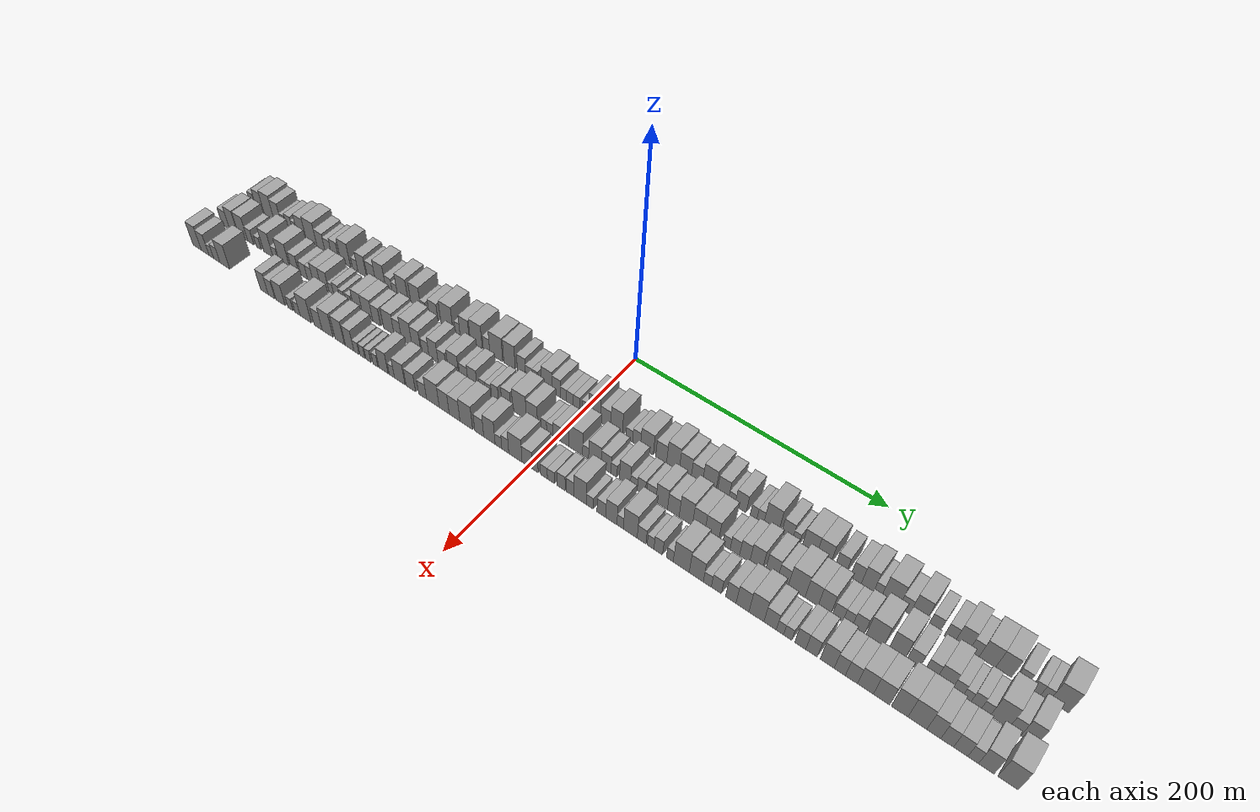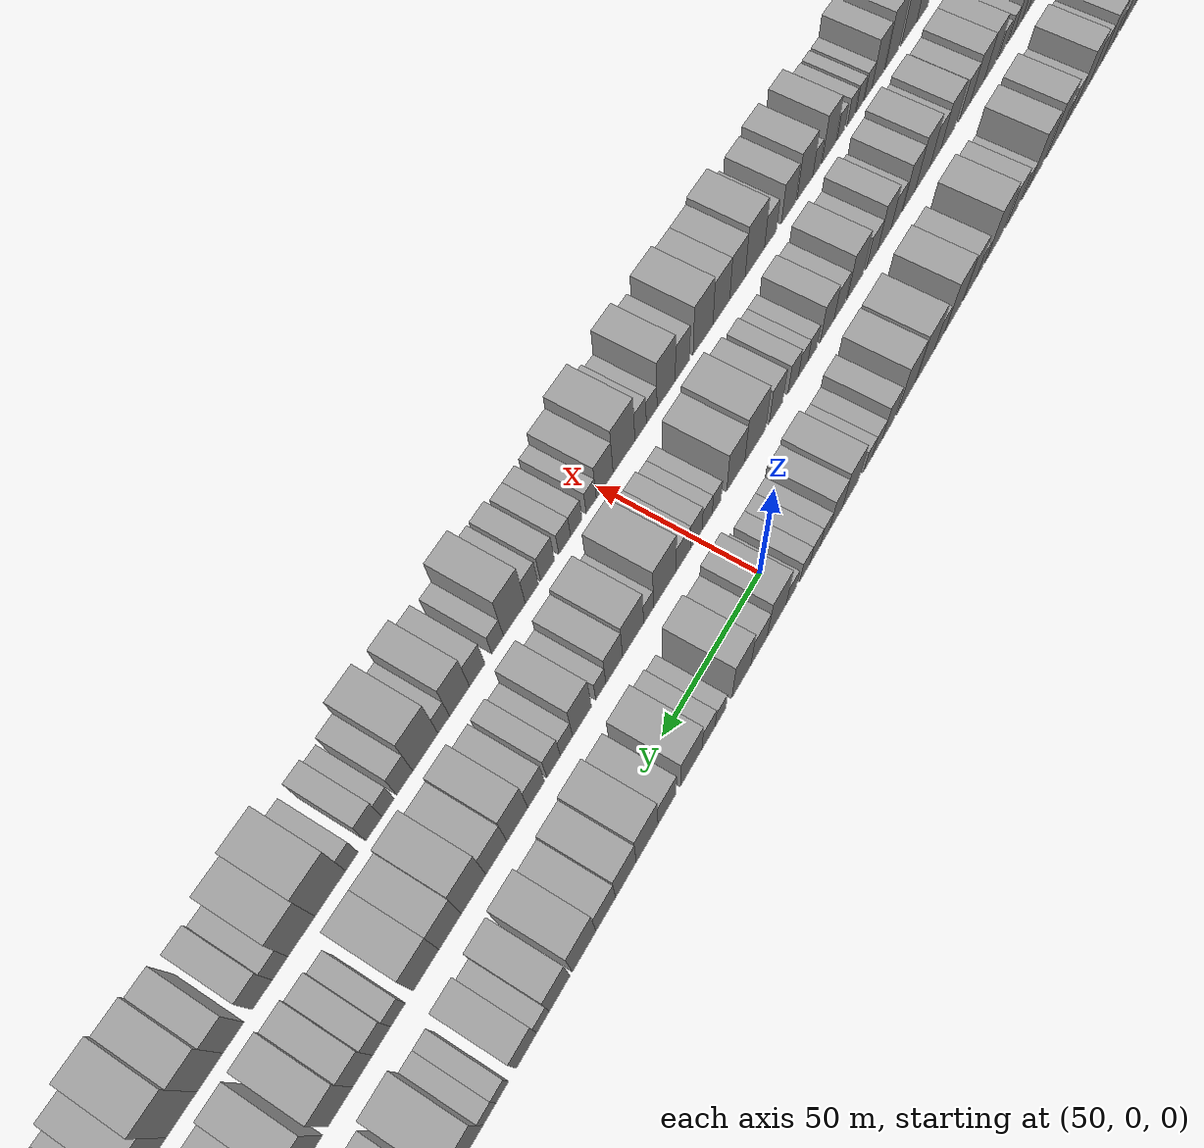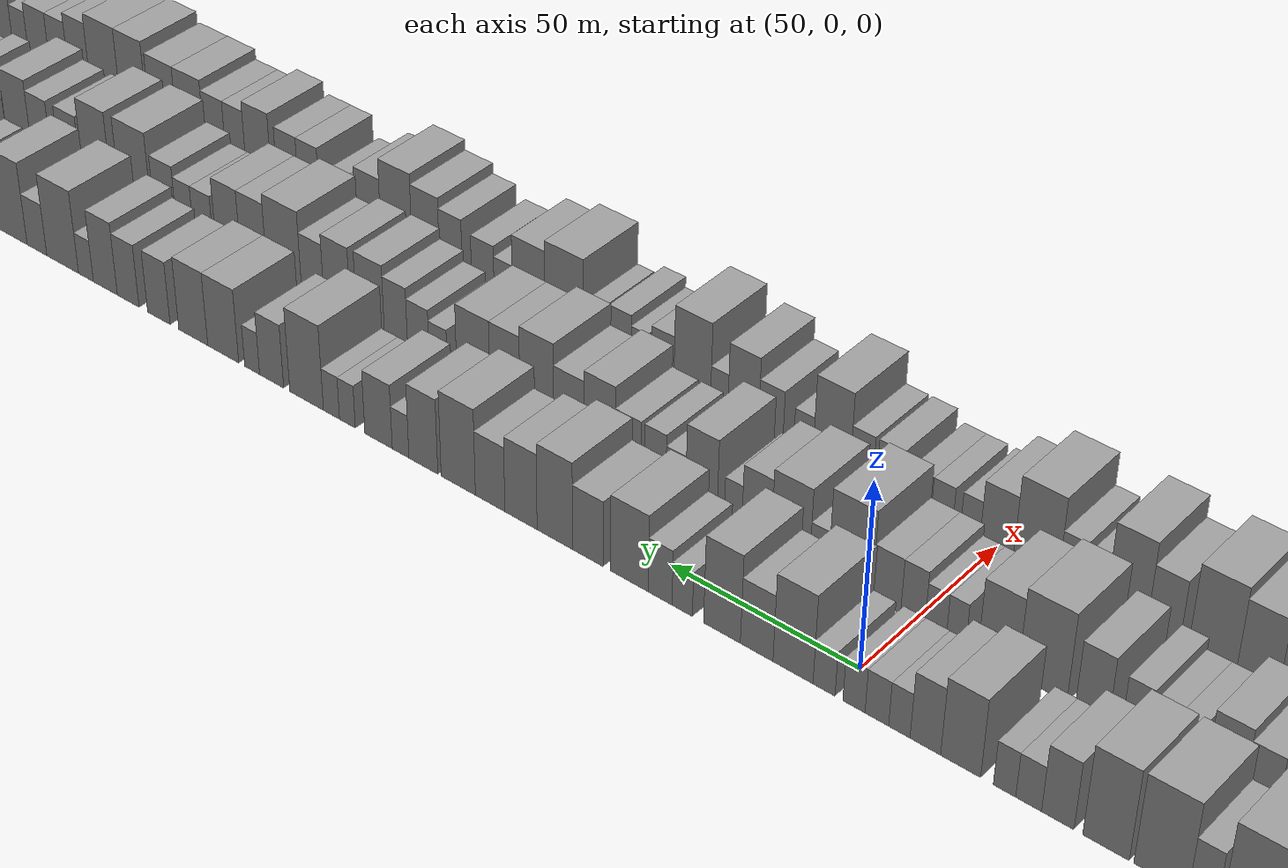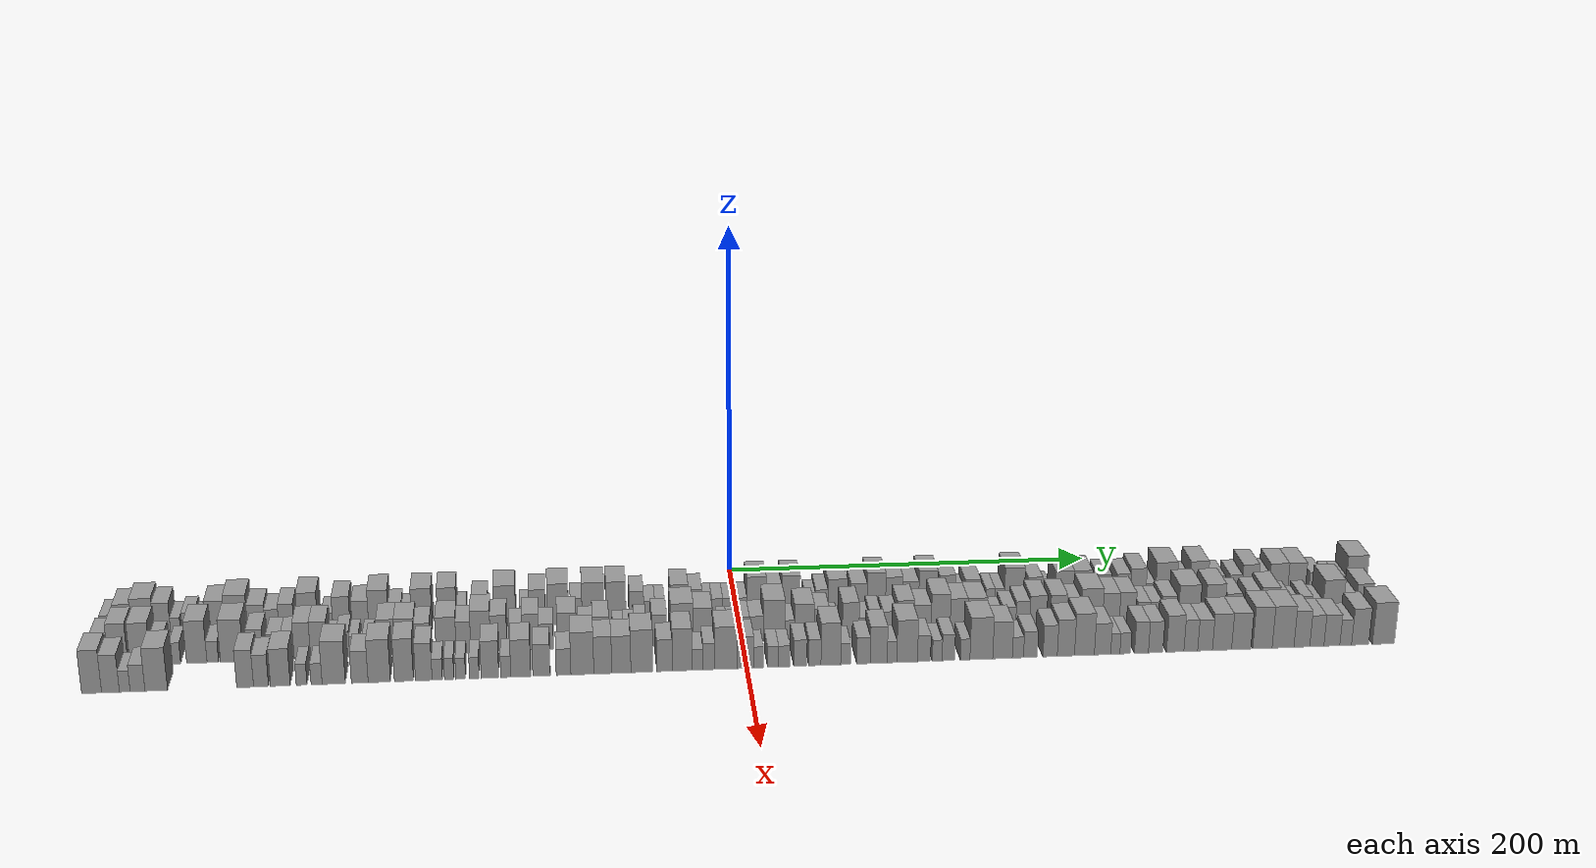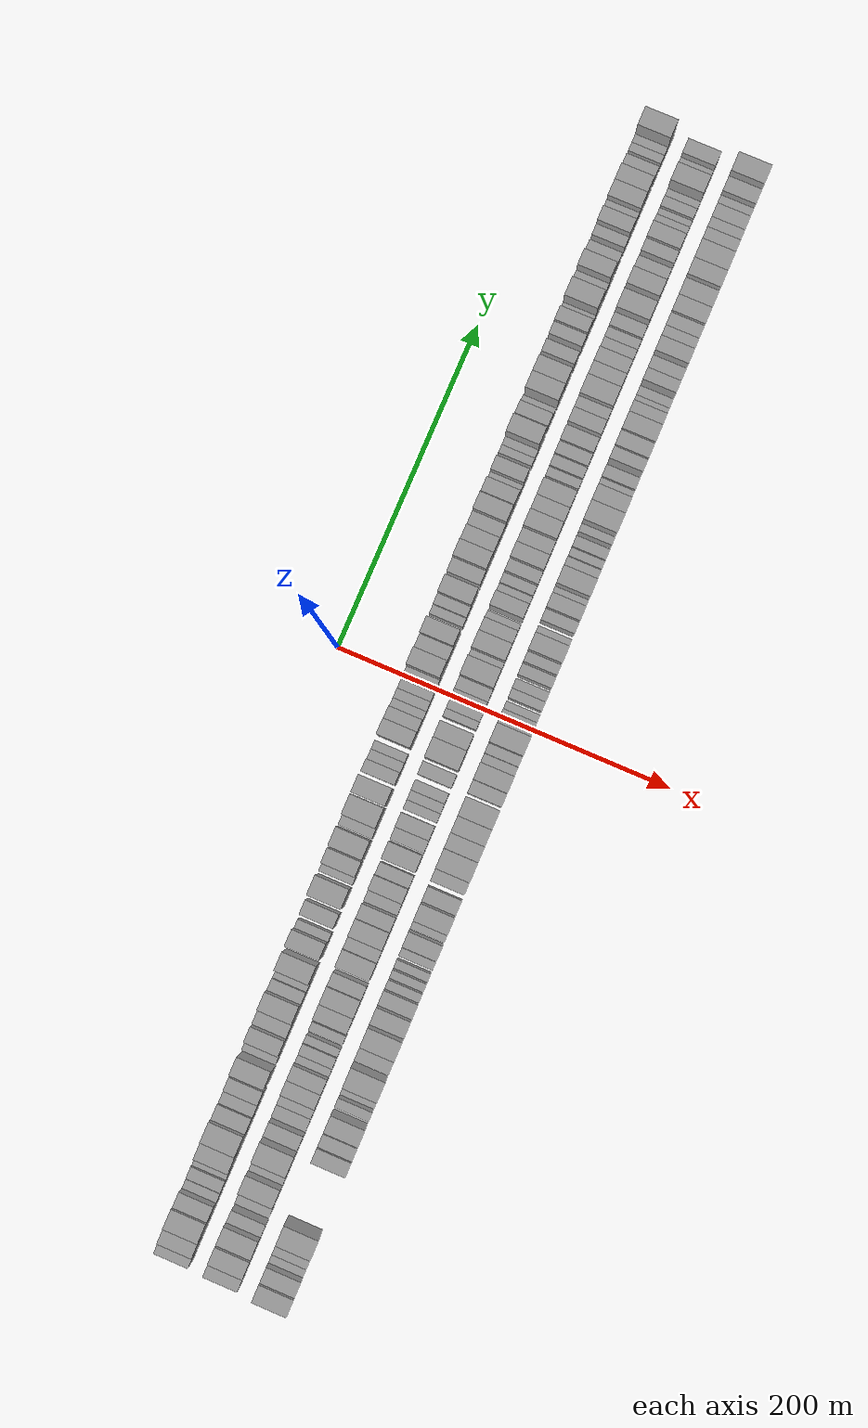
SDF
<sdf version="1.6">
 <world name="default">
  <scene>
   <sky><clouds><speed>12</speed></clouds></sky>
   <ambient>0.4 0.4 0.4 1</ambient>
   <background>0.7 0.7 0.7 1</background>
   <shadows>1</shadows>
  </scene>
  <gravity>0 0 -9.8066</gravity>
  <magnetic_field>6e-06 2.3e-05 -4.2e-05</magnetic_field>
  <physics default="0" name="default_physics" type="ode">
   <ode>
    <solver>
     <type>quick</type>
     <iters>10</iters>
     <sor>1.0</sor>
     <use_dynamic_moi_rescaling>0</use_dynamic_moi_rescaling>
    </solver>
    <constraints>
     <cfm>0</cfm>
     <erp>0.2</erp>
     <contact_max_correcting_vel>100</contact_max_correcting_vel>
     <contact_surface_layer>0.001</contact_surface_layer>
    </constraints>
   </ode>
   <max_step_size>0.004</max_step_size>
   <real_time_factor>1</real_time_factor>
   <real_time_update_rate>250</real_time_update_rate>
  </physics>
  <light name="sun" type="directional">
   <pose>0 0 10 0 0 0</pose>
   <diffuse>0.8 0.8 0.8 1</diffuse>
   <specular>0.2 0.2 0.2 1</specular>
   <attenuation>
    <range>1000</range>
    <constant>0.9</constant>
    <linear>0.01</linear>
    <quadratic>0.001</quadratic>
   </attenuation>
   <direction>-0.5 0.1 -0.9</direction>
  </light>
  <model name="building_1">
   <static>1</static>
   <pose>50.0000 -332.9522 0 0.000000 0.000000 0.000000</pose>
   <link name="link">
    <pose>0 0 7.50 0 0 0</pose>
    <collision name="collision"><geometry><box><size>20.0000 6.0955 15.0000</size></box></geometry></collision>
    <visual name="visual">
     <cast_shadows>0</cast_shadows>
     <geometry><box><size>20.0000 6.0955 15.0000</size></box></geometry>
     <material>
      <script>
       <uri>model://grey_wall/materials/scripts</uri>
       <uri>model://grey_wall/materials/textures</uri>
       <name>vrc/grey_wall</name>
      </script>
     </material>
    </visual>
   </link>
  </model>
  <model name="building_2">
   <static>1</static>
   <pose>50.0000 -324.4154 0 0.000000 0.000000 0.000000</pose>
   <link name="link">
    <pose>0 0 10.50 0 0 0</pose>
    <collision name="collision"><geometry><box><size>20.0000 8.9783 21.0000</size></box></geometry></collision>
    <visual name="visual">
     <cast_shadows>0</cast_shadows>
     <geometry><box><size>20.0000 8.9783 21.0000</size></box></geometry>
     <material>
      <script>
       <uri>model://grey_wall/materials/scripts</uri>
       <uri>model://grey_wall/materials/textures</uri>
       <name>vrc/grey_wall</name>
      </script>
     </material>
    </visual>
   </link>
  </model>
  <model name="building_3">
   <static>1</static>
   <pose>50.0000 -314.2920 0 0.000000 0.000000 0.000000</pose>
   <link name="link">
    <pose>0 0 12.00 0 0 0</pose>
    <collision name="collision"><geometry><box><size>20.0000 11.2685 24.0000</size></box></geometry></collision>
    <visual name="visual">
     <cast_shadows>0</cast_shadows>
     <geometry><box><size>20.0000 11.2685 24.0000</size></box></geometry>
     <material>
      <script>
       <uri>model://grey_wall/materials/scripts</uri>
       <uri>model://grey_wall/materials/textures</uri>
       <name>vrc/grey_wall</name>
      </script>
     </material>
    </visual>
   </link>
  </model>
  <model name="building_4">
   <static>1</static>
   <pose>50.0000 -304.2534 0 0.000000 0.000000 0.000000</pose>
   <link name="link">
    <pose>0 0 10.50 0 0 0</pose>
    <collision name="collision"><geometry><box><size>20.0000 8.8086 21.0000</size></box></geometry></collision>
    <visual name="visual">
     <cast_shadows>0</cast_shadows>
     <geometry><box><size>20.0000 8.8086 21.0000</size></box></geometry>
     <material>
      <script>
       <uri>model://grey_wall/materials/scripts</uri>
       <uri>model://grey_wall/materials/textures</uri>
       <name>vrc/grey_wall</name>
      </script>
     </material>
    </visual>
   </link>
  </model>
  <model name="building_5">
   <static>1</static>
   <pose>50.0000 -297.2645 0 0.000000 0.000000 0.000000</pose>
   <link name="link">
    <pose>0 0 6.00 0 0 0</pose>
    <collision name="collision"><geometry><box><size>20.0000 5.1691 12.0000</size></box></geometry></collision>
    <visual name="visual">
     <cast_shadows>0</cast_shadows>
     <geometry><box><size>20.0000 5.1691 12.0000</size></box></geometry>
     <material>
      <script>
       <uri>model://grey_wall/materials/scripts</uri>
       <uri>model://grey_wall/materials/textures</uri>
       <name>vrc/grey_wall</name>
      </script>
     </material>
    </visual>
   </link>
  </model>
  <model name="building_6">
   <static>1</static>
   <pose>50.0000 -290.2907 0 0.000000 0.000000 0.000000</pose>
   <link name="link">
    <pose>0 0 7.50 0 0 0</pose>
    <collision name="collision"><geometry><box><size>20.0000 6.7785 15.0000</size></box></geometry></collision>
    <visual name="visual">
     <cast_shadows>0</cast_shadows>
     <geometry><box><size>20.0000 6.7785 15.0000</size></box></geometry>
     <material>
      <script>
       <uri>model://grey_wall/materials/scripts</uri>
       <uri>model://grey_wall/materials/textures</uri>
       <name>vrc/grey_wall</name>
      </script>
     </material>
    </visual>
   </link>
  </model>
  <model name="building_7">
   <static>1</static>
   <pose>50.0000 -284.2733 0 0.000000 0.000000 0.000000</pose>
   <link name="link">
    <pose>0 0 6.00 0 0 0</pose>
    <collision name="collision"><geometry><box><size>20.0000 5.2564 12.0000</size></box></geometry></collision>
    <visual name="visual">
     <cast_shadows>0</cast_shadows>
     <geometry><box><size>20.0000 5.2564 12.0000</size></box></geometry>
     <material>
      <script>
       <uri>model://grey_wall/materials/scripts</uri>
       <uri>model://grey_wall/materials/textures</uri>
       <name>vrc/grey_wall</name>
      </script>
     </material>
    </visual>
   </link>
  </model>
  <model name="building_8">
   <static>1</static>
   <pose>50.0000 -276.6184 0 0.000000 0.000000 0.000000</pose>
   <link name="link">
    <pose>0 0 10.50 0 0 0</pose>
    <collision name="collision"><geometry><box><size>20.0000 10.0532 21.0000</size></box></geometry></collision>
    <visual name="visual">
     <cast_shadows>0</cast_shadows>
     <geometry><box><size>20.0000 10.0532 21.0000</size></box></geometry>
     <material>
      <script>
       <uri>model://grey_wall/materials/scripts</uri>
       <uri>model://grey_wall/materials/textures</uri>
       <name>vrc/grey_wall</name>
      </script>
     </material>
    </visual>
   </link>
  </model>
  <model name="building_9">
   <static>1</static>
   <pose>50.0000 -265.6870 0 0.000000 0.000000 0.000000</pose>
   <link name="link">
    <pose>0 0 12.00 0 0 0</pose>
    <collision name="collision"><geometry><box><size>20.0000 11.8096 24.0000</size></box></geometry></collision>
    <visual name="visual">
     <cast_shadows>0</cast_shadows>
     <geometry><box><size>20.0000 11.8096 24.0000</size></box></geometry>
     <material>
      <script>
       <uri>model://grey_wall/materials/scripts</uri>
       <uri>model://grey_wall/materials/textures</uri>
       <name>vrc/grey_wall</name>
      </script>
     </material>
    </visual>
   </link>
  </model>
  <model name="building_10">
   <static>1</static>
   <pose>50.0000 -255.3043 0 0.000000 0.000000 0.000000</pose>
   <link name="link">
    <pose>0 0 9.00 0 0 0</pose>
    <collision name="collision"><geometry><box><size>20.0000 8.9559 18.0000</size></box></geometry></collision>
    <visual name="visual">
     <cast_shadows>0</cast_shadows>
     <geometry><box><size>20.0000 8.9559 18.0000</size></box></geometry>
     <material>
      <script>
       <uri>model://grey_wall/materials/scripts</uri>
       <uri>model://grey_wall/materials/textures</uri>
       <name>vrc/grey_wall</name>
      </script>
     </material>
    </visual>
   </link>
  </model>
  <model name="building_11">
   <static>1</static>
   <pose>50.0000 -247.1612 0 0.000000 0.000000 0.000000</pose>
   <link name="link">
    <pose>0 0 7.50 0 0 0</pose>
    <collision name="collision"><geometry><box><size>20.0000 7.3303 15.0000</size></box></geometry></collision>
    <visual name="visual">
     <cast_shadows>0</cast_shadows>
     <geometry><box><size>20.0000 7.3303 15.0000</size></box></geometry>
     <material>
      <script>
       <uri>model://grey_wall/materials/scripts</uri>
       <uri>model://grey_wall/materials/textures</uri>
       <name>vrc/grey_wall</name>
      </script>
     </material>
    </visual>
   </link>
  </model>
  <model name="building_12">
   <static>1</static>
   <pose>50.0000 -239.5598 0 0.000000 0.000000 0.000000</pose>
   <link name="link">
    <pose>0 0 9.00 0 0 0</pose>
    <collision name="collision"><geometry><box><size>20.0000 7.8724 18.0000</size></box></geometry></collision>
    <visual name="visual">
     <cast_shadows>0</cast_shadows>
     <geometry><box><size>20.0000 7.8724 18.0000</size></box></geometry>
     <material>
      <script>
       <uri>model://grey_wall/materials/scripts</uri>
       <uri>model://grey_wall/materials/textures</uri>
       <name>vrc/grey_wall</name>
      </script>
     </material>
    </visual>
   </link>
  </model>
  <model name="building_13">
   <static>1</static>
   <pose>50.0000 -228.3800 0 0.000000 0.000000 0.000000</pose>
   <link name="link">
    <pose>0 0 12.00 0 0 0</pose>
    <collision name="collision"><geometry><box><size>20.0000 10.4870 24.0000</size></box></geometry></collision>
    <visual name="visual">
     <cast_shadows>0</cast_shadows>
     <geometry><box><size>20.0000 10.4870 24.0000</size></box></geometry>
     <material>
      <script>
       <uri>model://grey_wall/materials/scripts</uri>
       <uri>model://grey_wall/materials/textures</uri>
       <name>vrc/grey_wall</name>
      </script>
     </material>
    </visual>
   </link>
  </model>
  <model name="building_14">
   <static>1</static>
   <pose>50.0000 -218.1884 0 0.000000 0.000000 0.000000</pose>
   <link name="link">
    <pose>0 0 6.00 0 0 0</pose>
    <collision name="collision"><geometry><box><size>20.0000 5.8963 12.0000</size></box></geometry></collision>
    <visual name="visual">
     <cast_shadows>0</cast_shadows>
     <geometry><box><size>20.0000 5.8963 12.0000</size></box></geometry>
     <material>
      <script>
       <uri>model://grey_wall/materials/scripts</uri>
       <uri>model://grey_wall/materials/textures</uri>
       <name>vrc/grey_wall</name>
      </script>
     </material>
    </visual>
   </link>
  </model>
  <model name="building_15">
   <static>1</static>
   <pose>50.0000 -210.7343 0 0.000000 0.000000 0.000000</pose>
   <link name="link">
    <pose>0 0 10.50 0 0 0</pose>
    <collision name="collision"><geometry><box><size>20.0000 9.0119 21.0000</size></box></geometry></collision>
    <visual name="visual">
     <cast_shadows>0</cast_shadows>
     <geometry><box><size>20.0000 9.0119 21.0000</size></box></geometry>
     <material>
      <script>
       <uri>model://grey_wall/materials/scripts</uri>
       <uri>model://grey_wall/materials/textures</uri>
       <name>vrc/grey_wall</name>
      </script>
     </material>
    </visual>
   </link>
  </model>
  <model name="building_16">
   <static>1</static>
   <pose>50.0000 -200.8816 0 0.000000 0.000000 0.000000</pose>
   <link name="link">
    <pose>0 0 9.00 0 0 0</pose>
    <collision name="collision"><geometry><box><size>20.0000 8.6935 18.0000</size></box></geometry></collision>
    <visual name="visual">
     <cast_shadows>0</cast_shadows>
     <geometry><box><size>20.0000 8.6935 18.0000</size></box></geometry>
     <material>
      <script>
       <uri>model://grey_wall/materials/scripts</uri>
       <uri>model://grey_wall/materials/textures</uri>
       <name>vrc/grey_wall</name>
      </script>
     </material>
    </visual>
   </link>
  </model>
  <model name="building_17">
   <static>1</static>
   <pose>50.0000 -191.3085 0 0.000000 0.000000 0.000000</pose>
   <link name="link">
    <pose>0 0 12.00 0 0 0</pose>
    <collision name="collision"><geometry><box><size>20.0000 10.4528 24.0000</size></box></geometry></collision>
    <visual name="visual">
     <cast_shadows>0</cast_shadows>
     <geometry><box><size>20.0000 10.4528 24.0000</size></box></geometry>
     <material>
      <script>
       <uri>model://grey_wall/materials/scripts</uri>
       <uri>model://grey_wall/materials/textures</uri>
       <name>vrc/grey_wall</name>
      </script>
     </material>
    </visual>
   </link>
  </model>
  <model name="building_18">
   <static>1</static>
   <pose>50.0000 -182.6377 0 0.000000 0.000000 0.000000</pose>
   <link name="link">
    <pose>0 0 7.50 0 0 0</pose>
    <collision name="collision"><geometry><box><size>20.0000 6.8887 15.0000</size></box></geometry></collision>
    <visual name="visual">
     <cast_shadows>0</cast_shadows>
     <geometry><box><size>20.0000 6.8887 15.0000</size></box></geometry>
     <material>
      <script>
       <uri>model://grey_wall/materials/scripts</uri>
       <uri>model://grey_wall/materials/textures</uri>
       <name>vrc/grey_wall</name>
      </script>
     </material>
    </visual>
   </link>
  </model>
  <model name="building_19">
   <static>1</static>
   <pose>50.0000 -176.5488 0 0.000000 0.000000 0.000000</pose>
   <link name="link">
    <pose>0 0 6.00 0 0 0</pose>
    <collision name="collision"><geometry><box><size>20.0000 5.2893 12.0000</size></box></geometry></collision>
    <visual name="visual">
     <cast_shadows>0</cast_shadows>
     <geometry><box><size>20.0000 5.2893 12.0000</size></box></geometry>
     <material>
      <script>
       <uri>model://grey_wall/materials/scripts</uri>
       <uri>model://grey_wall/materials/textures</uri>
       <name>vrc/grey_wall</name>
      </script>
     </material>
    </visual>
   </link>
  </model>
  <model name="building_20">
   <static>1</static>
   <pose>50.0000 -168.5159 0 0.000000 0.000000 0.000000</pose>
   <link name="link">
    <pose>0 0 12.00 0 0 0</pose>
    <collision name="collision"><geometry><box><size>20.0000 10.7764 24.0000</size></box></geometry></collision>
    <visual name="visual">
     <cast_shadows>0</cast_shadows>
     <geometry><box><size>20.0000 10.7764 24.0000</size></box></geometry>
     <material>
      <script>
       <uri>model://grey_wall/materials/scripts</uri>
       <uri>model://grey_wall/materials/textures</uri>
       <name>vrc/grey_wall</name>
      </script>
     </material>
    </visual>
   </link>
  </model>
  <model name="building_21">
   <static>1</static>
   <pose>50.0000 -155.1342 0 0.000000 0.000000 0.000000</pose>
   <link name="link">
    <pose>0 0 12.00 0 0 0</pose>
    <collision name="collision"><geometry><box><size>20.0000 9.9871 24.0000</size></box></geometry></collision>
    <visual name="visual">
     <cast_shadows>0</cast_shadows>
     <geometry><box><size>20.0000 9.9871 24.0000</size></box></geometry>
     <material>
      <script>
       <uri>model://grey_wall/materials/scripts</uri>
       <uri>model://grey_wall/materials/textures</uri>
       <name>vrc/grey_wall</name>
      </script>
     </material>
    </visual>
   </link>
  </model>
  <model name="building_22">
   <static>1</static>
   <pose>50.0000 -147.5729 0 0.000000 0.000000 0.000000</pose>
   <link name="link">
    <pose>0 0 6.00 0 0 0</pose>
    <collision name="collision"><geometry><box><size>20.0000 5.1354 12.0000</size></box></geometry></collision>
    <visual name="visual">
     <cast_shadows>0</cast_shadows>
     <geometry><box><size>20.0000 5.1354 12.0000</size></box></geometry>
     <material>
      <script>
       <uri>model://grey_wall/materials/scripts</uri>
       <uri>model://grey_wall/materials/textures</uri>
       <name>vrc/grey_wall</name>
      </script>
     </material>
    </visual>
   </link>
  </model>
  <model name="building_23">
   <static>1</static>
   <pose>50.0000 -137.7555 0 0.000000 0.000000 0.000000</pose>
   <link name="link">
    <pose>0 0 9.00 0 0 0</pose>
    <collision name="collision"><geometry><box><size>20.0000 8.4995 18.0000</size></box></geometry></collision>
    <visual name="visual">
     <cast_shadows>0</cast_shadows>
     <geometry><box><size>20.0000 8.4995 18.0000</size></box></geometry>
     <material>
      <script>
       <uri>model://grey_wall/materials/scripts</uri>
       <uri>model://grey_wall/materials/textures</uri>
       <name>vrc/grey_wall</name>
      </script>
     </material>
    </visual>
   </link>
  </model>
  <model name="building_24">
   <static>1</static>
   <pose>50.0000 -124.6750 0 0.000000 0.000000 0.000000</pose>
   <link name="link">
    <pose>0 0 12.00 0 0 0</pose>
    <collision name="collision"><geometry><box><size>20.0000 11.6614 24.0000</size></box></geometry></collision>
    <visual name="visual">
     <cast_shadows>0</cast_shadows>
     <geometry><box><size>20.0000 11.6614 24.0000</size></box></geometry>
     <material>
      <script>
       <uri>model://grey_wall/materials/scripts</uri>
       <uri>model://grey_wall/materials/textures</uri>
       <name>vrc/grey_wall</name>
      </script>
     </material>
    </visual>
   </link>
  </model>
  <model name="building_25">
   <static>1</static>
   <pose>50.0000 -114.4293 0 0.000000 0.000000 0.000000</pose>
   <link name="link">
    <pose>0 0 6.00 0 0 0</pose>
    <collision name="collision"><geometry><box><size>20.0000 4.8299 12.0000</size></box></geometry></collision>
    <visual name="visual">
     <cast_shadows>0</cast_shadows>
     <geometry><box><size>20.0000 4.8299 12.0000</size></box></geometry>
     <material>
      <script>
       <uri>model://grey_wall/materials/scripts</uri>
       <uri>model://grey_wall/materials/textures</uri>
       <name>vrc/grey_wall</name>
      </script>
     </material>
    </visual>
   </link>
  </model>
  <model name="building_26">
   <static>1</static>
   <pose>50.0000 -107.5320 0 0.000000 0.000000 0.000000</pose>
   <link name="link">
    <pose>0 0 10.50 0 0 0</pose>
    <collision name="collision"><geometry><box><size>20.0000 8.9648 21.0000</size></box></geometry></collision>
    <visual name="visual">
     <cast_shadows>0</cast_shadows>
     <geometry><box><size>20.0000 8.9648 21.0000</size></box></geometry>
     <material>
      <script>
       <uri>model://grey_wall/materials/scripts</uri>
       <uri>model://grey_wall/materials/textures</uri>
       <name>vrc/grey_wall</name>
      </script>
     </material>
    </visual>
   </link>
  </model>
  <model name="building_27">
   <static>1</static>
   <pose>50.0000 -96.4396 0 0.000000 0.000000 0.000000</pose>
   <link name="link">
    <pose>0 0 12.00 0 0 0</pose>
    <collision name="collision"><geometry><box><size>20.0000 11.2199 24.0000</size></box></geometry></collision>
    <visual name="visual">
     <cast_shadows>0</cast_shadows>
     <geometry><box><size>20.0000 11.2199 24.0000</size></box></geometry>
     <material>
      <script>
       <uri>model://grey_wall/materials/scripts</uri>
       <uri>model://grey_wall/materials/textures</uri>
       <name>vrc/grey_wall</name>
      </script>
     </material>
    </visual>
   </link>
  </model>
  <model name="building_28">
   <static>1</static>
   <pose>50.0000 -86.7593 0 0.000000 0.000000 0.000000</pose>
   <link name="link">
    <pose>0 0 7.50 0 0 0</pose>
    <collision name="collision"><geometry><box><size>20.0000 6.1406 15.0000</size></box></geometry></collision>
    <visual name="visual">
     <cast_shadows>0</cast_shadows>
     <geometry><box><size>20.0000 6.1406 15.0000</size></box></geometry>
     <material>
      <script>
       <uri>model://grey_wall/materials/scripts</uri>
       <uri>model://grey_wall/materials/textures</uri>
       <name>vrc/grey_wall</name>
      </script>
     </material>
    </visual>
   </link>
  </model>
  <model name="building_29">
   <static>1</static>
   <pose>50.0000 -77.7071 0 0.000000 0.000000 0.000000</pose>
   <link name="link">
    <pose>0 0 12.00 0 0 0</pose>
    <collision name="collision"><geometry><box><size>20.0000 11.9637 24.0000</size></box></geometry></collision>
    <visual name="visual">
     <cast_shadows>0</cast_shadows>
     <geometry><box><size>20.0000 11.9637 24.0000</size></box></geometry>
     <material>
      <script>
       <uri>model://grey_wall/materials/scripts</uri>
       <uri>model://grey_wall/materials/textures</uri>
       <name>vrc/grey_wall</name>
      </script>
     </material>
    </visual>
   </link>
  </model>
  <model name="building_30">
   <static>1</static>
   <pose>50.0000 -65.4879 0 0.000000 0.000000 0.000000</pose>
   <link name="link">
    <pose>0 0 12.00 0 0 0</pose>
    <collision name="collision"><geometry><box><size>20.0000 10.4747 24.0000</size></box></geometry></collision>
    <visual name="visual">
     <cast_shadows>0</cast_shadows>
     <geometry><box><size>20.0000 10.4747 24.0000</size></box></geometry>
     <material>
      <script>
       <uri>model://grey_wall/materials/scripts</uri>
       <uri>model://grey_wall/materials/textures</uri>
       <name>vrc/grey_wall</name>
      </script>
     </material>
    </visual>
   </link>
  </model>
  <model name="building_31">
   <static>1</static>
   <pose>50.0000 -54.5210 0 0.000000 0.000000 0.000000</pose>
   <link name="link">
    <pose>0 0 9.00 0 0 0</pose>
    <collision name="collision"><geometry><box><size>20.0000 7.4592 18.0000</size></box></geometry></collision>
    <visual name="visual">
     <cast_shadows>0</cast_shadows>
     <geometry><box><size>20.0000 7.4592 18.0000</size></box></geometry>
     <material>
      <script>
       <uri>model://grey_wall/materials/scripts</uri>
       <uri>model://grey_wall/materials/textures</uri>
       <name>vrc/grey_wall</name>
      </script>
     </material>
    </visual>
   </link>
  </model>
  <model name="building_32">
   <static>1</static>
   <pose>50.0000 -47.8007 0 0.000000 0.000000 0.000000</pose>
   <link name="link">
    <pose>0 0 6.00 0 0 0</pose>
    <collision name="collision"><geometry><box><size>20.0000 5.9814 12.0000</size></box></geometry></collision>
    <visual name="visual">
     <cast_shadows>0</cast_shadows>
     <geometry><box><size>20.0000 5.9814 12.0000</size></box></geometry>
     <material>
      <script>
       <uri>model://grey_wall/materials/scripts</uri>
       <uri>model://grey_wall/materials/textures</uri>
       <name>vrc/grey_wall</name>
      </script>
     </material>
    </visual>
   </link>
  </model>
  <model name="building_33">
   <static>1</static>
   <pose>50.0000 -42.1817 0 0.000000 0.000000 0.000000</pose>
   <link name="link">
    <pose>0 0 6.00 0 0 0</pose>
    <collision name="collision"><geometry><box><size>20.0000 5.2565 12.0000</size></box></geometry></collision>
    <visual name="visual">
     <cast_shadows>0</cast_shadows>
     <geometry><box><size>20.0000 5.2565 12.0000</size></box></geometry>
     <material>
      <script>
       <uri>model://grey_wall/materials/scripts</uri>
       <uri>model://grey_wall/materials/textures</uri>
       <name>vrc/grey_wall</name>
      </script>
     </material>
    </visual>
   </link>
  </model>
  <model name="building_34">
   <static>1</static>
   <pose>50.0000 -31.7679 0 0.000000 0.000000 0.000000</pose>
   <link name="link">
    <pose>0 0 10.50 0 0 0</pose>
    <collision name="collision"><geometry><box><size>20.0000 9.5712 21.0000</size></box></geometry></collision>
    <visual name="visual">
     <cast_shadows>0</cast_shadows>
     <geometry><box><size>20.0000 9.5712 21.0000</size></box></geometry>
     <material>
      <script>
       <uri>model://grey_wall/materials/scripts</uri>
       <uri>model://grey_wall/materials/textures</uri>
       <name>vrc/grey_wall</name>
      </script>
     </material>
    </visual>
   </link>
  </model>
  <model name="building_35">
   <static>1</static>
   <pose>50.0000 -23.2715 0 0.000000 0.000000 0.000000</pose>
   <link name="link">
    <pose>0 0 9.00 0 0 0</pose>
    <collision name="collision"><geometry><box><size>20.0000 7.4215 18.0000</size></box></geometry></collision>
    <visual name="visual">
     <cast_shadows>0</cast_shadows>
     <geometry><box><size>20.0000 7.4215 18.0000</size></box></geometry>
     <material>
      <script>
       <uri>model://grey_wall/materials/scripts</uri>
       <uri>model://grey_wall/materials/textures</uri>
       <name>vrc/grey_wall</name>
      </script>
     </material>
    </visual>
   </link>
  </model>
  <model name="building_36">
   <static>1</static>
   <pose>50.0000 -16.9313 0 0.000000 0.000000 0.000000</pose>
   <link name="link">
    <pose>0 0 6.00 0 0 0</pose>
    <collision name="collision"><geometry><box><size>20.0000 5.2590 12.0000</size></box></geometry></collision>
    <visual name="visual">
     <cast_shadows>0</cast_shadows>
     <geometry><box><size>20.0000 5.2590 12.0000</size></box></geometry>
     <material>
      <script>
       <uri>model://grey_wall/materials/scripts</uri>
       <uri>model://grey_wall/materials/textures</uri>
       <name>vrc/grey_wall</name>
      </script>
     </material>
    </visual>
   </link>
  </model>
  <model name="building_37">
   <static>1</static>
   <pose>50.0000 -11.3831 0 0.000000 0.000000 0.000000</pose>
   <link name="link">
    <pose>0 0 6.00 0 0 0</pose>
    <collision name="collision"><geometry><box><size>20.0000 5.8374 12.0000</size></box></geometry></collision>
    <visual name="visual">
     <cast_shadows>0</cast_shadows>
     <geometry><box><size>20.0000 5.8374 12.0000</size></box></geometry>
     <material>
      <script>
       <uri>model://grey_wall/materials/scripts</uri>
       <uri>model://grey_wall/materials/textures</uri>
       <name>vrc/grey_wall</name>
      </script>
     </material>
    </visual>
   </link>
  </model>
  <model name="building_38">
   <static>1</static>
   <pose>50.0000 -5.7027 0 0.000000 0.000000 0.000000</pose>
   <link name="link">
    <pose>0 0 6.00 0 0 0</pose>
    <collision name="collision"><geometry><box><size>20.0000 5.5235 12.0000</size></box></geometry></collision>
    <visual name="visual">
     <cast_shadows>0</cast_shadows>
     <geometry><box><size>20.0000 5.5235 12.0000</size></box></geometry>
     <material>
      <script>
       <uri>model://grey_wall/materials/scripts</uri>
       <uri>model://grey_wall/materials/textures</uri>
       <name>vrc/grey_wall</name>
      </script>
     </material>
    </visual>
   </link>
  </model>
  <model name="building_39">
   <static>1</static>
   <pose>50.0000 1.8456 0 0.000000 0.000000 0.000000</pose>
   <link name="link">
    <pose>0 0 6.00 0 0 0</pose>
    <collision name="collision"><geometry><box><size>20.0000 5.5731 12.0000</size></box></geometry></collision>
    <visual name="visual">
     <cast_shadows>0</cast_shadows>
     <geometry><box><size>20.0000 5.5731 12.0000</size></box></geometry>
     <material>
      <script>
       <uri>model://grey_wall/materials/scripts</uri>
       <uri>model://grey_wall/materials/textures</uri>
       <name>vrc/grey_wall</name>
      </script>
     </material>
    </visual>
   </link>
  </model>
  <model name="building_40">
   <static>1</static>
   <pose>50.0000 9.7776 0 0.000000 0.000000 0.000000</pose>
   <link name="link">
    <pose>0 0 12.00 0 0 0</pose>
    <collision name="collision"><geometry><box><size>20.0000 10.2907 24.0000</size></box></geometry></collision>
    <visual name="visual">
     <cast_shadows>0</cast_shadows>
     <geometry><box><size>20.0000 10.2907 24.0000</size></box></geometry>
     <material>
      <script>
       <uri>model://grey_wall/materials/scripts</uri>
       <uri>model://grey_wall/materials/textures</uri>
       <name>vrc/grey_wall</name>
      </script>
     </material>
    </visual>
   </link>
  </model>
  <model name="building_41">
   <static>1</static>
   <pose>50.0000 19.1825 0 0.000000 0.000000 0.000000</pose>
   <link name="link">
    <pose>0 0 9.00 0 0 0</pose>
    <collision name="collision"><geometry><box><size>20.0000 8.5192 18.0000</size></box></geometry></collision>
    <visual name="visual">
     <cast_shadows>0</cast_shadows>
     <geometry><box><size>20.0000 8.5192 18.0000</size></box></geometry>
     <material>
      <script>
       <uri>model://grey_wall/materials/scripts</uri>
       <uri>model://grey_wall/materials/textures</uri>
       <name>vrc/grey_wall</name>
      </script>
     </material>
    </visual>
   </link>
  </model>
  <model name="building_42">
   <static>1</static>
   <pose>50.0000 28.3160 0 0.000000 0.000000 0.000000</pose>
   <link name="link">
    <pose>0 0 12.00 0 0 0</pose>
    <collision name="collision"><geometry><box><size>20.0000 9.7476 24.0000</size></box></geometry></collision>
    <visual name="visual">
     <cast_shadows>0</cast_shadows>
     <geometry><box><size>20.0000 9.7476 24.0000</size></box></geometry>
     <material>
      <script>
       <uri>model://grey_wall/materials/scripts</uri>
       <uri>model://grey_wall/materials/textures</uri>
       <name>vrc/grey_wall</name>
      </script>
     </material>
    </visual>
   </link>
  </model>
  <model name="building_43">
   <static>1</static>
   <pose>50.0000 38.9368 0 0.000000 0.000000 0.000000</pose>
   <link name="link">
    <pose>0 0 6.00 0 0 0</pose>
    <collision name="collision"><geometry><box><size>20.0000 5.4942 12.0000</size></box></geometry></collision>
    <visual name="visual">
     <cast_shadows>0</cast_shadows>
     <geometry><box><size>20.0000 5.4942 12.0000</size></box></geometry>
     <material>
      <script>
       <uri>model://grey_wall/materials/scripts</uri>
       <uri>model://grey_wall/materials/textures</uri>
       <name>vrc/grey_wall</name>
      </script>
     </material>
    </visual>
   </link>
  </model>
  <model name="building_44">
   <static>1</static>
   <pose>50.0000 44.9304 0 0.000000 0.000000 0.000000</pose>
   <link name="link">
    <pose>0 0 7.50 0 0 0</pose>
    <collision name="collision"><geometry><box><size>20.0000 6.4929 15.0000</size></box></geometry></collision>
    <visual name="visual">
     <cast_shadows>0</cast_shadows>
     <geometry><box><size>20.0000 6.4929 15.0000</size></box></geometry>
     <material>
      <script>
       <uri>model://grey_wall/materials/scripts</uri>
       <uri>model://grey_wall/materials/textures</uri>
       <name>vrc/grey_wall</name>
      </script>
     </material>
    </visual>
   </link>
  </model>
  <model name="building_45">
   <static>1</static>
   <pose>50.0000 53.4059 0 0.000000 0.000000 0.000000</pose>
   <link name="link">
    <pose>0 0 10.50 0 0 0</pose>
    <collision name="collision"><geometry><box><size>20.0000 10.4582 21.0000</size></box></geometry></collision>
    <visual name="visual">
     <cast_shadows>0</cast_shadows>
     <geometry><box><size>20.0000 10.4582 21.0000</size></box></geometry>
     <material>
      <script>
       <uri>model://grey_wall/materials/scripts</uri>
       <uri>model://grey_wall/materials/textures</uri>
       <name>vrc/grey_wall</name>
      </script>
     </material>
    </visual>
   </link>
  </model>
  <model name="building_46">
   <static>1</static>
   <pose>50.0000 64.9694 0 0.000000 0.000000 0.000000</pose>
   <link name="link">
    <pose>0 0 9.00 0 0 0</pose>
    <collision name="collision"><geometry><box><size>20.0000 8.6687 18.0000</size></box></geometry></collision>
    <visual name="visual">
     <cast_shadows>0</cast_shadows>
     <geometry><box><size>20.0000 8.6687 18.0000</size></box></geometry>
     <material>
      <script>
       <uri>model://grey_wall/materials/scripts</uri>
       <uri>model://grey_wall/materials/textures</uri>
       <name>vrc/grey_wall</name>
      </script>
     </material>
    </visual>
   </link>
  </model>
  <model name="building_47">
   <static>1</static>
   <pose>50.0000 74.3400 0 0.000000 0.000000 0.000000</pose>
   <link name="link">
    <pose>0 0 12.00 0 0 0</pose>
    <collision name="collision"><geometry><box><size>20.0000 10.0726 24.0000</size></box></geometry></collision>
    <visual name="visual">
     <cast_shadows>0</cast_shadows>
     <geometry><box><size>20.0000 10.0726 24.0000</size></box></geometry>
     <material>
      <script>
       <uri>model://grey_wall/materials/scripts</uri>
       <uri>model://grey_wall/materials/textures</uri>
       <name>vrc/grey_wall</name>
      </script>
     </material>
    </visual>
   </link>
  </model>
  <model name="building_48">
   <static>1</static>
   <pose>50.0000 84.0408 0 0.000000 0.000000 0.000000</pose>
   <link name="link">
    <pose>0 0 10.50 0 0 0</pose>
    <collision name="collision"><geometry><box><size>20.0000 9.3290 21.0000</size></box></geometry></collision>
    <visual name="visual">
     <cast_shadows>0</cast_shadows>
     <geometry><box><size>20.0000 9.3290 21.0000</size></box></geometry>
     <material>
      <script>
       <uri>model://grey_wall/materials/scripts</uri>
       <uri>model://grey_wall/materials/textures</uri>
       <name>vrc/grey_wall</name>
      </script>
     </material>
    </visual>
   </link>
  </model>
  <model name="building_49">
   <static>1</static>
   <pose>50.0000 93.0449 0 0.000000 0.000000 0.000000</pose>
   <link name="link">
    <pose>0 0 9.00 0 0 0</pose>
    <collision name="collision"><geometry><box><size>20.0000 8.6791 18.0000</size></box></geometry></collision>
    <visual name="visual">
     <cast_shadows>0</cast_shadows>
     <geometry><box><size>20.0000 8.6791 18.0000</size></box></geometry>
     <material>
      <script>
       <uri>model://grey_wall/materials/scripts</uri>
       <uri>model://grey_wall/materials/textures</uri>
       <name>vrc/grey_wall</name>
      </script>
     </material>
    </visual>
   </link>
  </model>
  <model name="building_50">
   <static>1</static>
   <pose>50.0000 102.5092 0 0.000000 0.000000 0.000000</pose>
   <link name="link">
    <pose>0 0 12.00 0 0 0</pose>
    <collision name="collision"><geometry><box><size>20.0000 10.2495 24.0000</size></box></geometry></collision>
    <visual name="visual">
     <cast_shadows>0</cast_shadows>
     <geometry><box><size>20.0000 10.2495 24.0000</size></box></geometry>
     <material>
      <script>
       <uri>model://grey_wall/materials/scripts</uri>
       <uri>model://grey_wall/materials/textures</uri>
       <name>vrc/grey_wall</name>
      </script>
     </material>
    </visual>
   </link>
  </model>
  <model name="building_51">
   <static>1</static>
   <pose>50.0000 113.0198 0 0.000000 0.000000 0.000000</pose>
   <link name="link">
    <pose>0 0 10.50 0 0 0</pose>
    <collision name="collision"><geometry><box><size>20.0000 8.7718 21.0000</size></box></geometry></collision>
    <visual name="visual">
     <cast_shadows>0</cast_shadows>
     <geometry><box><size>20.0000 8.7718 21.0000</size></box></geometry>
     <material>
      <script>
       <uri>model://grey_wall/materials/scripts</uri>
       <uri>model://grey_wall/materials/textures</uri>
       <name>vrc/grey_wall</name>
      </script>
     </material>
    </visual>
   </link>
  </model>
  <model name="building_52">
   <static>1</static>
   <pose>50.0000 119.9617 0 0.000000 0.000000 0.000000</pose>
   <link name="link">
    <pose>0 0 6.00 0 0 0</pose>
    <collision name="collision"><geometry><box><size>20.0000 5.1119 12.0000</size></box></geometry></collision>
    <visual name="visual">
     <cast_shadows>0</cast_shadows>
     <geometry><box><size>20.0000 5.1119 12.0000</size></box></geometry>
     <material>
      <script>
       <uri>model://grey_wall/materials/scripts</uri>
       <uri>model://grey_wall/materials/textures</uri>
       <name>vrc/grey_wall</name>
      </script>
     </material>
    </visual>
   </link>
  </model>
  <model name="building_53">
   <static>1</static>
   <pose>50.0000 126.7689 0 0.000000 0.000000 0.000000</pose>
   <link name="link">
    <pose>0 0 9.00 0 0 0</pose>
    <collision name="collision"><geometry><box><size>20.0000 8.5026 18.0000</size></box></geometry></collision>
    <visual name="visual">
     <cast_shadows>0</cast_shadows>
     <geometry><box><size>20.0000 8.5026 18.0000</size></box></geometry>
     <material>
      <script>
       <uri>model://grey_wall/materials/scripts</uri>
       <uri>model://grey_wall/materials/textures</uri>
       <name>vrc/grey_wall</name>
      </script>
     </material>
    </visual>
   </link>
  </model>
  <model name="building_54">
   <static>1</static>
   <pose>50.0000 136.5120 0 0.000000 0.000000 0.000000</pose>
   <link name="link">
    <pose>0 0 6.00 0 0 0</pose>
    <collision name="collision"><geometry><box><size>20.0000 4.9835 12.0000</size></box></geometry></collision>
    <visual name="visual">
     <cast_shadows>0</cast_shadows>
     <geometry><box><size>20.0000 4.9835 12.0000</size></box></geometry>
     <material>
      <script>
       <uri>model://grey_wall/materials/scripts</uri>
       <uri>model://grey_wall/materials/textures</uri>
       <name>vrc/grey_wall</name>
      </script>
     </material>
    </visual>
   </link>
  </model>
  <model name="building_55">
   <static>1</static>
   <pose>50.0000 141.5558 0 0.000000 0.000000 0.000000</pose>
   <link name="link">
    <pose>0 0 6.00 0 0 0</pose>
    <collision name="collision"><geometry><box><size>20.0000 5.1041 12.0000</size></box></geometry></collision>
    <visual name="visual">
     <cast_shadows>0</cast_shadows>
     <geometry><box><size>20.0000 5.1041 12.0000</size></box></geometry>
     <material>
      <script>
       <uri>model://grey_wall/materials/scripts</uri>
       <uri>model://grey_wall/materials/textures</uri>
       <name>vrc/grey_wall</name>
      </script>
     </material>
    </visual>
   </link>
  </model>
  <model name="building_56">
   <static>1</static>
   <pose>50.0000 149.5086 0 0.000000 0.000000 0.000000</pose>
   <link name="link">
    <pose>0 0 12.00 0 0 0</pose>
    <collision name="collision"><geometry><box><size>20.0000 10.8015 24.0000</size></box></geometry></collision>
    <visual name="visual">
     <cast_shadows>0</cast_shadows>
     <geometry><box><size>20.0000 10.8015 24.0000</size></box></geometry>
     <material>
      <script>
       <uri>model://grey_wall/materials/scripts</uri>
       <uri>model://grey_wall/materials/textures</uri>
       <name>vrc/grey_wall</name>
      </script>
     </material>
    </visual>
   </link>
  </model>
  <model name="building_57">
   <static>1</static>
   <pose>50.0000 160.8490 0 0.000000 0.000000 0.000000</pose>
   <link name="link">
    <pose>0 0 9.00 0 0 0</pose>
    <collision name="collision"><geometry><box><size>20.0000 7.8793 18.0000</size></box></geometry></collision>
    <visual name="visual">
     <cast_shadows>0</cast_shadows>
     <geometry><box><size>20.0000 7.8793 18.0000</size></box></geometry>
     <material>
      <script>
       <uri>model://grey_wall/materials/scripts</uri>
       <uri>model://grey_wall/materials/textures</uri>
       <name>vrc/grey_wall</name>
      </script>
     </material>
    </visual>
   </link>
  </model>
  <model name="building_58">
   <static>1</static>
   <pose>50.0000 167.2366 0 0.000000 0.000000 0.000000</pose>
   <link name="link">
    <pose>0 0 6.00 0 0 0</pose>
    <collision name="collision"><geometry><box><size>20.0000 4.8959 12.0000</size></box></geometry></collision>
    <visual name="visual">
     <cast_shadows>0</cast_shadows>
     <geometry><box><size>20.0000 4.8959 12.0000</size></box></geometry>
     <material>
      <script>
       <uri>model://grey_wall/materials/scripts</uri>
       <uri>model://grey_wall/materials/textures</uri>
       <name>vrc/grey_wall</name>
      </script>
     </material>
    </visual>
   </link>
  </model>
  <model name="building_59">
   <static>1</static>
   <pose>50.0000 176.8677 0 0.000000 0.000000 0.000000</pose>
   <link name="link">
    <pose>0 0 10.50 0 0 0</pose>
    <collision name="collision"><geometry><box><size>20.0000 10.3661 21.0000</size></box></geometry></collision>
    <visual name="visual">
     <cast_shadows>0</cast_shadows>
     <geometry><box><size>20.0000 10.3661 21.0000</size></box></geometry>
     <material>
      <script>
       <uri>model://grey_wall/materials/scripts</uri>
       <uri>model://grey_wall/materials/textures</uri>
       <name>vrc/grey_wall</name>
      </script>
     </material>
    </visual>
   </link>
  </model>
  <model name="building_60">
   <static>1</static>
   <pose>50.0000 186.9802 0 0.000000 0.000000 0.000000</pose>
   <link name="link">
    <pose>0 0 10.50 0 0 0</pose>
    <collision name="collision"><geometry><box><size>20.0000 9.8590 21.0000</size></box></geometry></collision>
    <visual name="visual">
     <cast_shadows>0</cast_shadows>
     <geometry><box><size>20.0000 9.8590 21.0000</size></box></geometry>
     <material>
      <script>
       <uri>model://grey_wall/materials/scripts</uri>
       <uri>model://grey_wall/materials/textures</uri>
       <name>vrc/grey_wall</name>
      </script>
     </material>
    </visual>
   </link>
  </model>
  <model name="building_61">
   <static>1</static>
   <pose>50.0000 198.7868 0 0.000000 0.000000 0.000000</pose>
   <link name="link">
    <pose>0 0 9.00 0 0 0</pose>
    <collision name="collision"><geometry><box><size>20.0000 7.7542 18.0000</size></box></geometry></collision>
    <visual name="visual">
     <cast_shadows>0</cast_shadows>
     <geometry><box><size>20.0000 7.7542 18.0000</size></box></geometry>
     <material>
      <script>
       <uri>model://grey_wall/materials/scripts</uri>
       <uri>model://grey_wall/materials/textures</uri>
       <name>vrc/grey_wall</name>
      </script>
     </material>
    </visual>
   </link>
  </model>
  <model name="building_62">
   <static>1</static>
   <pose>50.0000 209.4647 0 0.000000 0.000000 0.000000</pose>
   <link name="link">
    <pose>0 0 9.00 0 0 0</pose>
    <collision name="collision"><geometry><box><size>20.0000 7.6016 18.0000</size></box></geometry></collision>
    <visual name="visual">
     <cast_shadows>0</cast_shadows>
     <geometry><box><size>20.0000 7.6016 18.0000</size></box></geometry>
     <material>
      <script>
       <uri>model://grey_wall/materials/scripts</uri>
       <uri>model://grey_wall/materials/textures</uri>
       <name>vrc/grey_wall</name>
      </script>
     </material>
    </visual>
   </link>
  </model>
  <model name="building_63">
   <static>1</static>
   <pose>50.0000 217.5385 0 0.000000 0.000000 0.000000</pose>
   <link name="link">
    <pose>0 0 10.50 0 0 0</pose>
    <collision name="collision"><geometry><box><size>20.0000 8.5460 21.0000</size></box></geometry></collision>
    <visual name="visual">
     <cast_shadows>0</cast_shadows>
     <geometry><box><size>20.0000 8.5460 21.0000</size></box></geometry>
     <material>
      <script>
       <uri>model://grey_wall/materials/scripts</uri>
       <uri>model://grey_wall/materials/textures</uri>
       <name>vrc/grey_wall</name>
      </script>
     </material>
    </visual>
   </link>
  </model>
  <model name="building_64">
   <static>1</static>
   <pose>50.0000 224.4745 0 0.000000 0.000000 0.000000</pose>
   <link name="link">
    <pose>0 0 6.00 0 0 0</pose>
    <collision name="collision"><geometry><box><size>20.0000 5.3259 12.0000</size></box></geometry></collision>
    <visual name="visual">
     <cast_shadows>0</cast_shadows>
     <geometry><box><size>20.0000 5.3259 12.0000</size></box></geometry>
     <material>
      <script>
       <uri>model://grey_wall/materials/scripts</uri>
       <uri>model://grey_wall/materials/textures</uri>
       <name>vrc/grey_wall</name>
      </script>
     </material>
    </visual>
   </link>
  </model>
  <model name="building_65">
   <static>1</static>
   <pose>50.0000 232.9059 0 0.000000 0.000000 0.000000</pose>
   <link name="link">
    <pose>0 0 12.00 0 0 0</pose>
    <collision name="collision"><geometry><box><size>20.0000 11.5370 24.0000</size></box></geometry></collision>
    <visual name="visual">
     <cast_shadows>0</cast_shadows>
     <geometry><box><size>20.0000 11.5370 24.0000</size></box></geometry>
     <material>
      <script>
       <uri>model://grey_wall/materials/scripts</uri>
       <uri>model://grey_wall/materials/textures</uri>
       <name>vrc/grey_wall</name>
      </script>
     </material>
    </visual>
   </link>
  </model>
  <model name="building_66">
   <static>1</static>
   <pose>50.0000 242.2932 0 0.000000 0.000000 0.000000</pose>
   <link name="link">
    <pose>0 0 7.50 0 0 0</pose>
    <collision name="collision"><geometry><box><size>20.0000 7.2375 15.0000</size></box></geometry></collision>
    <visual name="visual">
     <cast_shadows>0</cast_shadows>
     <geometry><box><size>20.0000 7.2375 15.0000</size></box></geometry>
     <material>
      <script>
       <uri>model://grey_wall/materials/scripts</uri>
       <uri>model://grey_wall/materials/textures</uri>
       <name>vrc/grey_wall</name>
      </script>
     </material>
    </visual>
   </link>
  </model>
  <model name="building_67">
   <static>1</static>
   <pose>50.0000 250.8812 0 0.000000 0.000000 0.000000</pose>
   <link name="link">
    <pose>0 0 12.00 0 0 0</pose>
    <collision name="collision"><geometry><box><size>20.0000 9.9385 24.0000</size></box></geometry></collision>
    <visual name="visual">
     <cast_shadows>0</cast_shadows>
     <geometry><box><size>20.0000 9.9385 24.0000</size></box></geometry>
     <material>
      <script>
       <uri>model://grey_wall/materials/scripts</uri>
       <uri>model://grey_wall/materials/textures</uri>
       <name>vrc/grey_wall</name>
      </script>
     </material>
    </visual>
   </link>
  </model>
  <model name="building_68">
   <static>1</static>
   <pose>50.0000 261.5313 0 0.000000 0.000000 0.000000</pose>
   <link name="link">
    <pose>0 0 7.50 0 0 0</pose>
    <collision name="collision"><geometry><box><size>20.0000 7.3618 15.0000</size></box></geometry></collision>
    <visual name="visual">
     <cast_shadows>0</cast_shadows>
     <geometry><box><size>20.0000 7.3618 15.0000</size></box></geometry>
     <material>
      <script>
       <uri>model://grey_wall/materials/scripts</uri>
       <uri>model://grey_wall/materials/textures</uri>
       <name>vrc/grey_wall</name>
      </script>
     </material>
    </visual>
   </link>
  </model>
  <model name="building_69">
   <static>1</static>
   <pose>50.0000 271.6020 0 0.000000 0.000000 0.000000</pose>
   <link name="link">
    <pose>0 0 7.50 0 0 0</pose>
    <collision name="collision"><geometry><box><size>20.0000 6.7797 15.0000</size></box></geometry></collision>
    <visual name="visual">
     <cast_shadows>0</cast_shadows>
     <geometry><box><size>20.0000 6.7797 15.0000</size></box></geometry>
     <material>
      <script>
       <uri>model://grey_wall/materials/scripts</uri>
       <uri>model://grey_wall/materials/textures</uri>
       <name>vrc/grey_wall</name>
      </script>
     </material>
    </visual>
   </link>
  </model>
  <model name="building_70">
   <static>1</static>
   <pose>50.0000 279.4677 0 0.000000 0.000000 0.000000</pose>
   <link name="link">
    <pose>0 0 10.50 0 0 0</pose>
    <collision name="collision"><geometry><box><size>20.0000 8.9516 21.0000</size></box></geometry></collision>
    <visual name="visual">
     <cast_shadows>0</cast_shadows>
     <geometry><box><size>20.0000 8.9516 21.0000</size></box></geometry>
     <material>
      <script>
       <uri>model://grey_wall/materials/scripts</uri>
       <uri>model://grey_wall/materials/textures</uri>
       <name>vrc/grey_wall</name>
      </script>
     </material>
    </visual>
   </link>
  </model>
  <model name="building_71">
   <static>1</static>
   <pose>50.0000 287.0806 0 0.000000 0.000000 0.000000</pose>
   <link name="link">
    <pose>0 0 7.50 0 0 0</pose>
    <collision name="collision"><geometry><box><size>20.0000 6.2743 15.0000</size></box></geometry></collision>
    <visual name="visual">
     <cast_shadows>0</cast_shadows>
     <geometry><box><size>20.0000 6.2743 15.0000</size></box></geometry>
     <material>
      <script>
       <uri>model://grey_wall/materials/scripts</uri>
       <uri>model://grey_wall/materials/textures</uri>
       <name>vrc/grey_wall</name>
      </script>
     </material>
    </visual>
   </link>
  </model>
  <model name="building_72">
   <static>1</static>
   <pose>50.0000 295.3811 0 0.000000 0.000000 0.000000</pose>
   <link name="link">
    <pose>0 0 10.50 0 0 0</pose>
    <collision name="collision"><geometry><box><size>20.0000 10.3266 21.0000</size></box></geometry></collision>
    <visual name="visual">
     <cast_shadows>0</cast_shadows>
     <geometry><box><size>20.0000 10.3266 21.0000</size></box></geometry>
     <material>
      <script>
       <uri>model://grey_wall/materials/scripts</uri>
       <uri>model://grey_wall/materials/textures</uri>
       <name>vrc/grey_wall</name>
      </script>
     </material>
    </visual>
   </link>
  </model>
  <model name="building_73">
   <static>1</static>
   <pose>50.0000 305.4804 0 0.000000 0.000000 0.000000</pose>
   <link name="link">
    <pose>0 0 10.50 0 0 0</pose>
    <collision name="collision"><geometry><box><size>20.0000 9.8720 21.0000</size></box></geometry></collision>
    <visual name="visual">
     <cast_shadows>0</cast_shadows>
     <geometry><box><size>20.0000 9.8720 21.0000</size></box></geometry>
     <material>
      <script>
       <uri>model://grey_wall/materials/scripts</uri>
       <uri>model://grey_wall/materials/textures</uri>
       <name>vrc/grey_wall</name>
      </script>
     </material>
    </visual>
   </link>
  </model>
  <model name="building_74">
   <static>1</static>
   <pose>50.0000 315.9014 0 0.000000 0.000000 0.000000</pose>
   <link name="link">
    <pose>0 0 7.50 0 0 0</pose>
    <collision name="collision"><geometry><box><size>20.0000 6.9698 15.0000</size></box></geometry></collision>
    <visual name="visual">
     <cast_shadows>0</cast_shadows>
     <geometry><box><size>20.0000 6.9698 15.0000</size></box></geometry>
     <material>
      <script>
       <uri>model://grey_wall/materials/scripts</uri>
       <uri>model://grey_wall/materials/textures</uri>
       <name>vrc/grey_wall</name>
      </script>
     </material>
    </visual>
   </link>
  </model>
  <model name="building_75">
   <static>1</static>
   <pose>50.0000 325.0619 0 0.000000 0.000000 0.000000</pose>
   <link name="link">
    <pose>0 0 6.00 0 0 0</pose>
    <collision name="collision"><geometry><box><size>20.0000 5.3513 12.0000</size></box></geometry></collision>
    <visual name="visual">
     <cast_shadows>0</cast_shadows>
     <geometry><box><size>20.0000 5.3513 12.0000</size></box></geometry>
     <material>
      <script>
       <uri>model://grey_wall/materials/scripts</uri>
       <uri>model://grey_wall/materials/textures</uri>
       <name>vrc/grey_wall</name>
      </script>
     </material>
    </visual>
   </link>
  </model>
  <model name="building_76">
   <static>1</static>
   <pose>50.0000 330.3383 0 0.000000 0.000000 0.000000</pose>
   <link name="link">
    <pose>0 0 6.00 0 0 0</pose>
    <collision name="collision"><geometry><box><size>20.0000 5.2015 12.0000</size></box></geometry></collision>
    <visual name="visual">
     <cast_shadows>0</cast_shadows>
     <geometry><box><size>20.0000 5.2015 12.0000</size></box></geometry>
     <material>
      <script>
       <uri>model://grey_wall/materials/scripts</uri>
       <uri>model://grey_wall/materials/textures</uri>
       <name>vrc/grey_wall</name>
      </script>
     </material>
    </visual>
   </link>
  </model>
  <model name="building_77">
   <static>1</static>
   <pose>50.0000 338.7043 0 0.000000 0.000000 0.000000</pose>
   <link name="link">
    <pose>0 0 12.00 0 0 0</pose>
    <collision name="collision"><geometry><box><size>20.0000 11.5305 24.0000</size></box></geometry></collision>
    <visual name="visual">
     <cast_shadows>0</cast_shadows>
     <geometry><box><size>20.0000 11.5305 24.0000</size></box></geometry>
     <material>
      <script>
       <uri>model://grey_wall/materials/scripts</uri>
       <uri>model://grey_wall/materials/textures</uri>
       <name>vrc/grey_wall</name>
      </script>
     </material>
    </visual>
   </link>
  </model>
  <model name="building_78">
   <static>1</static>
   <pose>79.0000 -331.7164 0 0.000000 0.000000 0.000000</pose>
   <link name="link">
    <pose>0 0 9.00 0 0 0</pose>
    <collision name="collision"><geometry><box><size>20.0000 8.5672 18.0000</size></box></geometry></collision>
    <visual name="visual">
     <cast_shadows>0</cast_shadows>
     <geometry><box><size>20.0000 8.5672 18.0000</size></box></geometry>
     <material>
      <script>
       <uri>model://grey_wall/materials/scripts</uri>
       <uri>model://grey_wall/materials/textures</uri>
       <name>vrc/grey_wall</name>
      </script>
     </material>
    </visual>
   </link>
  </model>
  <model name="building_79">
   <static>1</static>
   <pose>79.0000 -322.5121 0 0.000000 0.000000 0.000000</pose>
   <link name="link">
    <pose>0 0 12.00 0 0 0</pose>
    <collision name="collision"><geometry><box><size>20.0000 9.8414 24.0000</size></box></geometry></collision>
    <visual name="visual">
     <cast_shadows>0</cast_shadows>
     <geometry><box><size>20.0000 9.8414 24.0000</size></box></geometry>
     <material>
      <script>
       <uri>model://grey_wall/materials/scripts</uri>
       <uri>model://grey_wall/materials/textures</uri>
       <name>vrc/grey_wall</name>
      </script>
     </material>
    </visual>
   </link>
  </model>
  <model name="building_80">
   <static>1</static>
   <pose>79.0000 -311.3957 0 0.000000 0.000000 0.000000</pose>
   <link name="link">
    <pose>0 0 12.00 0 0 0</pose>
    <collision name="collision"><geometry><box><size>20.0000 10.3913 24.0000</size></box></geometry></collision>
    <visual name="visual">
     <cast_shadows>0</cast_shadows>
     <geometry><box><size>20.0000 10.3913 24.0000</size></box></geometry>
     <material>
      <script>
       <uri>model://grey_wall/materials/scripts</uri>
       <uri>model://grey_wall/materials/textures</uri>
       <name>vrc/grey_wall</name>
      </script>
     </material>
    </visual>
   </link>
  </model>
  <model name="building_81">
   <static>1</static>
   <pose>79.0000 -302.7373 0 0.000000 0.000000 0.000000</pose>
   <link name="link">
    <pose>0 0 7.50 0 0 0</pose>
    <collision name="collision"><geometry><box><size>20.0000 6.9254 15.0000</size></box></geometry></collision>
    <visual name="visual">
     <cast_shadows>0</cast_shadows>
     <geometry><box><size>20.0000 6.9254 15.0000</size></box></geometry>
     <material>
      <script>
       <uri>model://grey_wall/materials/scripts</uri>
       <uri>model://grey_wall/materials/textures</uri>
       <name>vrc/grey_wall</name>
      </script>
     </material>
    </visual>
   </link>
  </model>
  <model name="building_82">
   <static>1</static>
   <pose>79.0000 -293.6001 0 0.000000 0.000000 0.000000</pose>
   <link name="link">
    <pose>0 0 6.00 0 0 0</pose>
    <collision name="collision"><geometry><box><size>20.0000 5.3490 12.0000</size></box></geometry></collision>
    <visual name="visual">
     <cast_shadows>0</cast_shadows>
     <geometry><box><size>20.0000 5.3490 12.0000</size></box></geometry>
     <material>
      <script>
       <uri>model://grey_wall/materials/scripts</uri>
       <uri>model://grey_wall/materials/textures</uri>
       <name>vrc/grey_wall</name>
      </script>
     </material>
    </visual>
   </link>
  </model>
  <model name="building_83">
   <static>1</static>
   <pose>79.0000 -282.7220 0 0.000000 0.000000 0.000000</pose>
   <link name="link">
    <pose>0 0 12.00 0 0 0</pose>
    <collision name="collision"><geometry><box><size>20.0000 10.4072 24.0000</size></box></geometry></collision>
    <visual name="visual">
     <cast_shadows>0</cast_shadows>
     <geometry><box><size>20.0000 10.4072 24.0000</size></box></geometry>
     <material>
      <script>
       <uri>model://grey_wall/materials/scripts</uri>
       <uri>model://grey_wall/materials/textures</uri>
       <name>vrc/grey_wall</name>
      </script>
     </material>
    </visual>
   </link>
  </model>
  <model name="building_84">
   <static>1</static>
   <pose>79.0000 -274.5836 0 0.000000 0.000000 0.000000</pose>
   <link name="link">
    <pose>0 0 6.00 0 0 0</pose>
    <collision name="collision"><geometry><box><size>20.0000 5.8697 12.0000</size></box></geometry></collision>
    <visual name="visual">
     <cast_shadows>0</cast_shadows>
     <geometry><box><size>20.0000 5.8697 12.0000</size></box></geometry>
     <material>
      <script>
       <uri>model://grey_wall/materials/scripts</uri>
       <uri>model://grey_wall/materials/textures</uri>
       <name>vrc/grey_wall</name>
      </script>
     </material>
    </visual>
   </link>
  </model>
  <model name="building_85">
   <static>1</static>
   <pose>79.0000 -264.7724 0 0.000000 0.000000 0.000000</pose>
   <link name="link">
    <pose>0 0 12.00 0 0 0</pose>
    <collision name="collision"><geometry><box><size>20.0000 11.7528 24.0000</size></box></geometry></collision>
    <visual name="visual">
     <cast_shadows>0</cast_shadows>
     <geometry><box><size>20.0000 11.7528 24.0000</size></box></geometry>
     <material>
      <script>
       <uri>model://grey_wall/materials/scripts</uri>
       <uri>model://grey_wall/materials/textures</uri>
       <name>vrc/grey_wall</name>
      </script>
     </material>
    </visual>
   </link>
  </model>
  <model name="building_86">
   <static>1</static>
   <pose>79.0000 -252.7841 0 0.000000 0.000000 0.000000</pose>
   <link name="link">
    <pose>0 0 9.00 0 0 0</pose>
    <collision name="collision"><geometry><box><size>20.0000 8.2237 18.0000</size></box></geometry></collision>
    <visual name="visual">
     <cast_shadows>0</cast_shadows>
     <geometry><box><size>20.0000 8.2237 18.0000</size></box></geometry>
     <material>
      <script>
       <uri>model://grey_wall/materials/scripts</uri>
       <uri>model://grey_wall/materials/textures</uri>
       <name>vrc/grey_wall</name>
      </script>
     </material>
    </visual>
   </link>
  </model>
  <model name="building_87">
   <static>1</static>
   <pose>79.0000 -243.0189 0 0.000000 0.000000 0.000000</pose>
   <link name="link">
    <pose>0 0 7.50 0 0 0</pose>
    <collision name="collision"><geometry><box><size>20.0000 7.3068 15.0000</size></box></geometry></collision>
    <visual name="visual">
     <cast_shadows>0</cast_shadows>
     <geometry><box><size>20.0000 7.3068 15.0000</size></box></geometry>
     <material>
      <script>
       <uri>model://grey_wall/materials/scripts</uri>
       <uri>model://grey_wall/materials/textures</uri>
       <name>vrc/grey_wall</name>
      </script>
     </material>
    </visual>
   </link>
  </model>
  <model name="building_88">
   <static>1</static>
   <pose>79.0000 -236.1746 0 0.000000 0.000000 0.000000</pose>
   <link name="link">
    <pose>0 0 7.50 0 0 0</pose>
    <collision name="collision"><geometry><box><size>20.0000 6.3819 15.0000</size></box></geometry></collision>
    <visual name="visual">
     <cast_shadows>0</cast_shadows>
     <geometry><box><size>20.0000 6.3819 15.0000</size></box></geometry>
     <material>
      <script>
       <uri>model://grey_wall/materials/scripts</uri>
       <uri>model://grey_wall/materials/textures</uri>
       <name>vrc/grey_wall</name>
      </script>
     </material>
    </visual>
   </link>
  </model>
  <model name="building_89">
   <static>1</static>
   <pose>79.0000 -228.7768 0 0.000000 0.000000 0.000000</pose>
   <link name="link">
    <pose>0 0 10.50 0 0 0</pose>
    <collision name="collision"><geometry><box><size>20.0000 8.4136 21.0000</size></box></geometry></collision>
    <visual name="visual">
     <cast_shadows>0</cast_shadows>
     <geometry><box><size>20.0000 8.4136 21.0000</size></box></geometry>
     <material>
      <script>
       <uri>model://grey_wall/materials/scripts</uri>
       <uri>model://grey_wall/materials/textures</uri>
       <name>vrc/grey_wall</name>
      </script>
     </material>
    </visual>
   </link>
  </model>
  <model name="building_90">
   <static>1</static>
   <pose>79.0000 -220.2091 0 0.000000 0.000000 0.000000</pose>
   <link name="link">
    <pose>0 0 10.50 0 0 0</pose>
    <collision name="collision"><geometry><box><size>20.0000 8.7219 21.0000</size></box></geometry></collision>
    <visual name="visual">
     <cast_shadows>0</cast_shadows>
     <geometry><box><size>20.0000 8.7219 21.0000</size></box></geometry>
     <material>
      <script>
       <uri>model://grey_wall/materials/scripts</uri>
       <uri>model://grey_wall/materials/textures</uri>
       <name>vrc/grey_wall</name>
      </script>
     </material>
    </visual>
   </link>
  </model>
  <model name="building_91">
   <static>1</static>
   <pose>79.0000 -213.3384 0 0.000000 0.000000 0.000000</pose>
   <link name="link">
    <pose>0 0 6.00 0 0 0</pose>
    <collision name="collision"><geometry><box><size>20.0000 5.0196 12.0000</size></box></geometry></collision>
    <visual name="visual">
     <cast_shadows>0</cast_shadows>
     <geometry><box><size>20.0000 5.0196 12.0000</size></box></geometry>
     <material>
      <script>
       <uri>model://grey_wall/materials/scripts</uri>
       <uri>model://grey_wall/materials/textures</uri>
       <name>vrc/grey_wall</name>
      </script>
     </material>
    </visual>
   </link>
  </model>
  <model name="building_92">
   <static>1</static>
   <pose>79.0000 -207.6542 0 0.000000 0.000000 0.000000</pose>
   <link name="link">
    <pose>0 0 7.50 0 0 0</pose>
    <collision name="collision"><geometry><box><size>20.0000 6.3489 15.0000</size></box></geometry></collision>
    <visual name="visual">
     <cast_shadows>0</cast_shadows>
     <geometry><box><size>20.0000 6.3489 15.0000</size></box></geometry>
     <material>
      <script>
       <uri>model://grey_wall/materials/scripts</uri>
       <uri>model://grey_wall/materials/textures</uri>
       <name>vrc/grey_wall</name>
      </script>
     </material>
    </visual>
   </link>
  </model>
  <model name="building_93">
   <static>1</static>
   <pose>79.0000 -202.0791 0 0.000000 0.000000 0.000000</pose>
   <link name="link">
    <pose>0 0 6.00 0 0 0</pose>
    <collision name="collision"><geometry><box><size>20.0000 4.8012 12.0000</size></box></geometry></collision>
    <visual name="visual">
     <cast_shadows>0</cast_shadows>
     <geometry><box><size>20.0000 4.8012 12.0000</size></box></geometry>
     <material>
      <script>
       <uri>model://grey_wall/materials/scripts</uri>
       <uri>model://grey_wall/materials/textures</uri>
       <name>vrc/grey_wall</name>
      </script>
     </material>
    </visual>
   </link>
  </model>
  <model name="building_94">
   <static>1</static>
   <pose>79.0000 -194.9390 0 0.000000 0.000000 0.000000</pose>
   <link name="link">
    <pose>0 0 6.00 0 0 0</pose>
    <collision name="collision"><geometry><box><size>20.0000 5.4791 12.0000</size></box></geometry></collision>
    <visual name="visual">
     <cast_shadows>0</cast_shadows>
     <geometry><box><size>20.0000 5.4791 12.0000</size></box></geometry>
     <material>
      <script>
       <uri>model://grey_wall/materials/scripts</uri>
       <uri>model://grey_wall/materials/textures</uri>
       <name>vrc/grey_wall</name>
      </script>
     </material>
    </visual>
   </link>
  </model>
  <model name="building_95">
   <static>1</static>
   <pose>79.0000 -185.7063 0 0.000000 0.000000 0.000000</pose>
   <link name="link">
    <pose>0 0 10.50 0 0 0</pose>
    <collision name="collision"><geometry><box><size>20.0000 8.9863 21.0000</size></box></geometry></collision>
    <visual name="visual">
     <cast_shadows>0</cast_shadows>
     <geometry><box><size>20.0000 8.9863 21.0000</size></box></geometry>
     <material>
      <script>
       <uri>model://grey_wall/materials/scripts</uri>
       <uri>model://grey_wall/materials/textures</uri>
       <name>vrc/grey_wall</name>
      </script>
     </material>
    </visual>
   </link>
  </model>
  <model name="building_96">
   <static>1</static>
   <pose>79.0000 -176.0860 0 0.000000 0.000000 0.000000</pose>
   <link name="link">
    <pose>0 0 10.50 0 0 0</pose>
    <collision name="collision"><geometry><box><size>20.0000 10.2544 21.0000</size></box></geometry></collision>
    <visual name="visual">
     <cast_shadows>0</cast_shadows>
     <geometry><box><size>20.0000 10.2544 21.0000</size></box></geometry>
     <material>
      <script>
       <uri>model://grey_wall/materials/scripts</uri>
       <uri>model://grey_wall/materials/textures</uri>
       <name>vrc/grey_wall</name>
      </script>
     </material>
    </visual>
   </link>
  </model>
  <model name="building_97">
   <static>1</static>
   <pose>79.0000 -166.9662 0 0.000000 0.000000 0.000000</pose>
   <link name="link">
    <pose>0 0 9.00 0 0 0</pose>
    <collision name="collision"><geometry><box><size>20.0000 7.9852 18.0000</size></box></geometry></collision>
    <visual name="visual">
     <cast_shadows>0</cast_shadows>
     <geometry><box><size>20.0000 7.9852 18.0000</size></box></geometry>
     <material>
      <script>
       <uri>model://grey_wall/materials/scripts</uri>
       <uri>model://grey_wall/materials/textures</uri>
       <name>vrc/grey_wall</name>
      </script>
     </material>
    </visual>
   </link>
  </model>
  <model name="building_98">
   <static>1</static>
   <pose>79.0000 -154.7618 0 0.000000 0.000000 0.000000</pose>
   <link name="link">
    <pose>0 0 10.50 0 0 0</pose>
    <collision name="collision"><geometry><box><size>20.0000 10.4234 21.0000</size></box></geometry></collision>
    <visual name="visual">
     <cast_shadows>0</cast_shadows>
     <geometry><box><size>20.0000 10.4234 21.0000</size></box></geometry>
     <material>
      <script>
       <uri>model://grey_wall/materials/scripts</uri>
       <uri>model://grey_wall/materials/textures</uri>
       <name>vrc/grey_wall</name>
      </script>
     </material>
    </visual>
   </link>
  </model>
  <model name="building_99">
   <static>1</static>
   <pose>79.0000 -145.7677 0 0.000000 0.000000 0.000000</pose>
   <link name="link">
    <pose>0 0 9.00 0 0 0</pose>
    <collision name="collision"><geometry><box><size>20.0000 7.5649 18.0000</size></box></geometry></collision>
    <visual name="visual">
     <cast_shadows>0</cast_shadows>
     <geometry><box><size>20.0000 7.5649 18.0000</size></box></geometry>
     <material>
      <script>
       <uri>model://grey_wall/materials/scripts</uri>
       <uri>model://grey_wall/materials/textures</uri>
       <name>vrc/grey_wall</name>
      </script>
     </material>
    </visual>
   </link>
  </model>
  <model name="building_100">
   <static>1</static>
   <pose>79.0000 -136.8499 0 0.000000 0.000000 0.000000</pose>
   <link name="link">
    <pose>0 0 12.00 0 0 0</pose>
    <collision name="collision"><geometry><box><size>20.0000 10.2707 24.0000</size></box></geometry></collision>
    <visual name="visual">
     <cast_shadows>0</cast_shadows>
     <geometry><box><size>20.0000 10.2707 24.0000</size></box></geometry>
     <material>
      <script>
       <uri>model://grey_wall/materials/scripts</uri>
       <uri>model://grey_wall/materials/textures</uri>
       <name>vrc/grey_wall</name>
      </script>
     </material>
    </visual>
   </link>
  </model>
  <model name="building_101">
   <static>1</static>
   <pose>79.0000 -127.4600 0 0.000000 0.000000 0.000000</pose>
   <link name="link">
    <pose>0 0 10.50 0 0 0</pose>
    <collision name="collision"><geometry><box><size>20.0000 8.5091 21.0000</size></box></geometry></collision>
    <visual name="visual">
     <cast_shadows>0</cast_shadows>
     <geometry><box><size>20.0000 8.5091 21.0000</size></box></geometry>
     <material>
      <script>
       <uri>model://grey_wall/materials/scripts</uri>
       <uri>model://grey_wall/materials/textures</uri>
       <name>vrc/grey_wall</name>
      </script>
     </material>
    </visual>
   </link>
  </model>
  <model name="building_102">
   <static>1</static>
   <pose>79.0000 -118.7304 0 0.000000 0.000000 0.000000</pose>
   <link name="link">
    <pose>0 0 7.50 0 0 0</pose>
    <collision name="collision"><geometry><box><size>20.0000 6.9502 15.0000</size></box></geometry></collision>
    <visual name="visual">
     <cast_shadows>0</cast_shadows>
     <geometry><box><size>20.0000 6.9502 15.0000</size></box></geometry>
     <material>
      <script>
       <uri>model://grey_wall/materials/scripts</uri>
       <uri>model://grey_wall/materials/textures</uri>
       <name>vrc/grey_wall</name>
      </script>
     </material>
    </visual>
   </link>
  </model>
  <model name="building_103">
   <static>1</static>
   <pose>79.0000 -110.9171 0 0.000000 0.000000 0.000000</pose>
   <link name="link">
    <pose>0 0 10.50 0 0 0</pose>
    <collision name="collision"><geometry><box><size>20.0000 8.6764 21.0000</size></box></geometry></collision>
    <visual name="visual">
     <cast_shadows>0</cast_shadows>
     <geometry><box><size>20.0000 8.6764 21.0000</size></box></geometry>
     <material>
      <script>
       <uri>model://grey_wall/materials/scripts</uri>
       <uri>model://grey_wall/materials/textures</uri>
       <name>vrc/grey_wall</name>
      </script>
     </material>
    </visual>
   </link>
  </model>
  <model name="building_104">
   <static>1</static>
   <pose>79.0000 -102.8480 0 0.000000 0.000000 0.000000</pose>
   <link name="link">
    <pose>0 0 7.50 0 0 0</pose>
    <collision name="collision"><geometry><box><size>20.0000 7.4617 15.0000</size></box></geometry></collision>
    <visual name="visual">
     <cast_shadows>0</cast_shadows>
     <geometry><box><size>20.0000 7.4617 15.0000</size></box></geometry>
     <material>
      <script>
       <uri>model://grey_wall/materials/scripts</uri>
       <uri>model://grey_wall/materials/textures</uri>
       <name>vrc/grey_wall</name>
      </script>
     </material>
    </visual>
   </link>
  </model>
  <model name="building_105">
   <static>1</static>
   <pose>79.0000 -92.0790 0 0.000000 0.000000 0.000000</pose>
   <link name="link">
    <pose>0 0 10.50 0 0 0</pose>
    <collision name="collision"><geometry><box><size>20.0000 10.0763 21.0000</size></box></geometry></collision>
    <visual name="visual">
     <cast_shadows>0</cast_shadows>
     <geometry><box><size>20.0000 10.0763 21.0000</size></box></geometry>
     <material>
      <script>
       <uri>model://grey_wall/materials/scripts</uri>
       <uri>model://grey_wall/materials/textures</uri>
       <name>vrc/grey_wall</name>
      </script>
     </material>
    </visual>
   </link>
  </model>
  <model name="building_106">
   <static>1</static>
   <pose>79.0000 -82.3220 0 0.000000 0.000000 0.000000</pose>
   <link name="link">
    <pose>0 0 7.50 0 0 0</pose>
    <collision name="collision"><geometry><box><size>20.0000 7.4376 15.0000</size></box></geometry></collision>
    <visual name="visual">
     <cast_shadows>0</cast_shadows>
     <geometry><box><size>20.0000 7.4376 15.0000</size></box></geometry>
     <material>
      <script>
       <uri>model://grey_wall/materials/scripts</uri>
       <uri>model://grey_wall/materials/textures</uri>
       <name>vrc/grey_wall</name>
      </script>
     </material>
    </visual>
   </link>
  </model>
  <model name="building_107">
   <static>1</static>
   <pose>79.0000 -74.3436 0 0.000000 0.000000 0.000000</pose>
   <link name="link">
    <pose>0 0 9.00 0 0 0</pose>
    <collision name="collision"><geometry><box><size>20.0000 8.5192 18.0000</size></box></geometry></collision>
    <visual name="visual">
     <cast_shadows>0</cast_shadows>
     <geometry><box><size>20.0000 8.5192 18.0000</size></box></geometry>
     <material>
      <script>
       <uri>model://grey_wall/materials/scripts</uri>
       <uri>model://grey_wall/materials/textures</uri>
       <name>vrc/grey_wall</name>
      </script>
     </material>
    </visual>
   </link>
  </model>
  <model name="building_108">
   <static>1</static>
   <pose>79.0000 -65.3470 0 0.000000 0.000000 0.000000</pose>
   <link name="link">
    <pose>0 0 6.00 0 0 0</pose>
    <collision name="collision"><geometry><box><size>20.0000 5.4741 12.0000</size></box></geometry></collision>
    <visual name="visual">
     <cast_shadows>0</cast_shadows>
     <geometry><box><size>20.0000 5.4741 12.0000</size></box></geometry>
     <material>
      <script>
       <uri>model://grey_wall/materials/scripts</uri>
       <uri>model://grey_wall/materials/textures</uri>
       <name>vrc/grey_wall</name>
      </script>
     </material>
    </visual>
   </link>
  </model>
  <model name="building_109">
   <static>1</static>
   <pose>79.0000 -59.7610 0 0.000000 0.000000 0.000000</pose>
   <link name="link">
    <pose>0 0 6.00 0 0 0</pose>
    <collision name="collision"><geometry><box><size>20.0000 5.6979 12.0000</size></box></geometry></collision>
    <visual name="visual">
     <cast_shadows>0</cast_shadows>
     <geometry><box><size>20.0000 5.6979 12.0000</size></box></geometry>
     <material>
      <script>
       <uri>model://grey_wall/materials/scripts</uri>
       <uri>model://grey_wall/materials/textures</uri>
       <name>vrc/grey_wall</name>
      </script>
     </material>
    </visual>
   </link>
  </model>
  <model name="building_110">
   <static>1</static>
   <pose>79.0000 -53.7962 0 0.000000 0.000000 0.000000</pose>
   <link name="link">
    <pose>0 0 7.50 0 0 0</pose>
    <collision name="collision"><geometry><box><size>20.0000 6.2316 15.0000</size></box></geometry></collision>
    <visual name="visual">
     <cast_shadows>0</cast_shadows>
     <geometry><box><size>20.0000 6.2316 15.0000</size></box></geometry>
     <material>
      <script>
       <uri>model://grey_wall/materials/scripts</uri>
       <uri>model://grey_wall/materials/textures</uri>
       <name>vrc/grey_wall</name>
      </script>
     </material>
    </visual>
   </link>
  </model>
  <model name="building_111">
   <static>1</static>
   <pose>79.0000 -43.7526 0 0.000000 0.000000 0.000000</pose>
   <link name="link">
    <pose>0 0 9.00 0 0 0</pose>
    <collision name="collision"><geometry><box><size>20.0000 7.8557 18.0000</size></box></geometry></collision>
    <visual name="visual">
     <cast_shadows>0</cast_shadows>
     <geometry><box><size>20.0000 7.8557 18.0000</size></box></geometry>
     <material>
      <script>
       <uri>model://grey_wall/materials/scripts</uri>
       <uri>model://grey_wall/materials/textures</uri>
       <name>vrc/grey_wall</name>
      </script>
     </material>
    </visual>
   </link>
  </model>
  <model name="building_112">
   <static>1</static>
   <pose>79.0000 -31.8844 0 0.000000 0.000000 0.000000</pose>
   <link name="link">
    <pose>0 0 12.00 0 0 0</pose>
    <collision name="collision"><geometry><box><size>20.0000 11.8805 24.0000</size></box></geometry></collision>
    <visual name="visual">
     <cast_shadows>0</cast_shadows>
     <geometry><box><size>20.0000 11.8805 24.0000</size></box></geometry>
     <material>
      <script>
       <uri>model://grey_wall/materials/scripts</uri>
       <uri>model://grey_wall/materials/textures</uri>
       <name>vrc/grey_wall</name>
      </script>
     </material>
    </visual>
   </link>
  </model>
  <model name="building_113">
   <static>1</static>
   <pose>79.0000 -20.9908 0 0.000000 0.000000 0.000000</pose>
   <link name="link">
    <pose>0 0 10.50 0 0 0</pose>
    <collision name="collision"><geometry><box><size>20.0000 9.9066 21.0000</size></box></geometry></collision>
    <visual name="visual">
     <cast_shadows>0</cast_shadows>
     <geometry><box><size>20.0000 9.9066 21.0000</size></box></geometry>
     <material>
      <script>
       <uri>model://grey_wall/materials/scripts</uri>
       <uri>model://grey_wall/materials/textures</uri>
       <name>vrc/grey_wall</name>
      </script>
     </material>
    </visual>
   </link>
  </model>
  <model name="building_114">
   <static>1</static>
   <pose>79.0000 -10.6145 0 0.000000 0.000000 0.000000</pose>
   <link name="link">
    <pose>0 0 6.00 0 0 0</pose>
    <collision name="collision"><geometry><box><size>20.0000 4.8462 12.0000</size></box></geometry></collision>
    <visual name="visual">
     <cast_shadows>0</cast_shadows>
     <geometry><box><size>20.0000 4.8462 12.0000</size></box></geometry>
     <material>
      <script>
       <uri>model://grey_wall/materials/scripts</uri>
       <uri>model://grey_wall/materials/textures</uri>
       <name>vrc/grey_wall</name>
      </script>
     </material>
    </visual>
   </link>
  </model>
  <model name="building_115">
   <static>1</static>
   <pose>79.0000 -5.4730 0 0.000000 0.000000 0.000000</pose>
   <link name="link">
    <pose>0 0 6.00 0 0 0</pose>
    <collision name="collision"><geometry><box><size>20.0000 5.4368 12.0000</size></box></geometry></collision>
    <visual name="visual">
     <cast_shadows>0</cast_shadows>
     <geometry><box><size>20.0000 5.4368 12.0000</size></box></geometry>
     <material>
      <script>
       <uri>model://grey_wall/materials/scripts</uri>
       <uri>model://grey_wall/materials/textures</uri>
       <name>vrc/grey_wall</name>
      </script>
     </material>
    </visual>
   </link>
  </model>
  <model name="building_116">
   <static>1</static>
   <pose>79.0000 0.3407 0 0.000000 0.000000 0.000000</pose>
   <link name="link">
    <pose>0 0 7.50 0 0 0</pose>
    <collision name="collision"><geometry><box><size>20.0000 6.1906 15.0000</size></box></geometry></collision>
    <visual name="visual">
     <cast_shadows>0</cast_shadows>
     <geometry><box><size>20.0000 6.1906 15.0000</size></box></geometry>
     <material>
      <script>
       <uri>model://grey_wall/materials/scripts</uri>
       <uri>model://grey_wall/materials/textures</uri>
       <name>vrc/grey_wall</name>
      </script>
     </material>
    </visual>
   </link>
  </model>
  <model name="building_117">
   <static>1</static>
   <pose>79.0000 7.1395 0 0.000000 0.000000 0.000000</pose>
   <link name="link">
    <pose>0 0 7.50 0 0 0</pose>
    <collision name="collision"><geometry><box><size>20.0000 7.4070 15.0000</size></box></geometry></collision>
    <visual name="visual">
     <cast_shadows>0</cast_shadows>
     <geometry><box><size>20.0000 7.4070 15.0000</size></box></geometry>
     <material>
      <script>
       <uri>model://grey_wall/materials/scripts</uri>
       <uri>model://grey_wall/materials/textures</uri>
       <name>vrc/grey_wall</name>
      </script>
     </material>
    </visual>
   </link>
  </model>
  <model name="building_118">
   <static>1</static>
   <pose>79.0000 16.5934 0 0.000000 0.000000 0.000000</pose>
   <link name="link">
    <pose>0 0 12.00 0 0 0</pose>
    <collision name="collision"><geometry><box><size>20.0000 11.5009 24.0000</size></box></geometry></collision>
    <visual name="visual">
     <cast_shadows>0</cast_shadows>
     <geometry><box><size>20.0000 11.5009 24.0000</size></box></geometry>
     <material>
      <script>
       <uri>model://grey_wall/materials/scripts</uri>
       <uri>model://grey_wall/materials/textures</uri>
       <name>vrc/grey_wall</name>
      </script>
     </material>
    </visual>
   </link>
  </model>
  <model name="building_119">
   <static>1</static>
   <pose>79.0000 24.8157 0 0.000000 0.000000 0.000000</pose>
   <link name="link">
    <pose>0 0 6.00 0 0 0</pose>
    <collision name="collision"><geometry><box><size>20.0000 4.9436 12.0000</size></box></geometry></collision>
    <visual name="visual">
     <cast_shadows>0</cast_shadows>
     <geometry><box><size>20.0000 4.9436 12.0000</size></box></geometry>
     <material>
      <script>
       <uri>model://grey_wall/materials/scripts</uri>
       <uri>model://grey_wall/materials/textures</uri>
       <name>vrc/grey_wall</name>
      </script>
     </material>
    </visual>
   </link>
  </model>
  <model name="building_120">
   <static>1</static>
   <pose>79.0000 32.4561 0 0.000000 0.000000 0.000000</pose>
   <link name="link">
    <pose>0 0 10.50 0 0 0</pose>
    <collision name="collision"><geometry><box><size>20.0000 10.3373 21.0000</size></box></geometry></collision>
    <visual name="visual">
     <cast_shadows>0</cast_shadows>
     <geometry><box><size>20.0000 10.3373 21.0000</size></box></geometry>
     <material>
      <script>
       <uri>model://grey_wall/materials/scripts</uri>
       <uri>model://grey_wall/materials/textures</uri>
       <name>vrc/grey_wall</name>
      </script>
     </material>
    </visual>
   </link>
  </model>
  <model name="building_121">
   <static>1</static>
   <pose>79.0000 41.6530 0 0.000000 0.000000 0.000000</pose>
   <link name="link">
    <pose>0 0 9.00 0 0 0</pose>
    <collision name="collision"><geometry><box><size>20.0000 8.0564 18.0000</size></box></geometry></collision>
    <visual name="visual">
     <cast_shadows>0</cast_shadows>
     <geometry><box><size>20.0000 8.0564 18.0000</size></box></geometry>
     <material>
      <script>
       <uri>model://grey_wall/materials/scripts</uri>
       <uri>model://grey_wall/materials/textures</uri>
       <name>vrc/grey_wall</name>
      </script>
     </material>
    </visual>
   </link>
  </model>
  <model name="building_122">
   <static>1</static>
   <pose>79.0000 48.1084 0 0.000000 0.000000 0.000000</pose>
   <link name="link">
    <pose>0 0 6.00 0 0 0</pose>
    <collision name="collision"><geometry><box><size>20.0000 4.8543 12.0000</size></box></geometry></collision>
    <visual name="visual">
     <cast_shadows>0</cast_shadows>
     <geometry><box><size>20.0000 4.8543 12.0000</size></box></geometry>
     <material>
      <script>
       <uri>model://grey_wall/materials/scripts</uri>
       <uri>model://grey_wall/materials/textures</uri>
       <name>vrc/grey_wall</name>
      </script>
     </material>
    </visual>
   </link>
  </model>
  <model name="building_123">
   <static>1</static>
   <pose>79.0000 56.9386 0 0.000000 0.000000 0.000000</pose>
   <link name="link">
    <pose>0 0 10.50 0 0 0</pose>
    <collision name="collision"><geometry><box><size>20.0000 8.8061 21.0000</size></box></geometry></collision>
    <visual name="visual">
     <cast_shadows>0</cast_shadows>
     <geometry><box><size>20.0000 8.8061 21.0000</size></box></geometry>
     <material>
      <script>
       <uri>model://grey_wall/materials/scripts</uri>
       <uri>model://grey_wall/materials/textures</uri>
       <name>vrc/grey_wall</name>
      </script>
     </material>
    </visual>
   </link>
  </model>
  <model name="building_124">
   <static>1</static>
   <pose>79.0000 64.1504 0 0.000000 0.000000 0.000000</pose>
   <link name="link">
    <pose>0 0 6.00 0 0 0</pose>
    <collision name="collision"><geometry><box><size>20.0000 5.6175 12.0000</size></box></geometry></collision>
    <visual name="visual">
     <cast_shadows>0</cast_shadows>
     <geometry><box><size>20.0000 5.6175 12.0000</size></box></geometry>
     <material>
      <script>
       <uri>model://grey_wall/materials/scripts</uri>
       <uri>model://grey_wall/materials/textures</uri>
       <name>vrc/grey_wall</name>
      </script>
     </material>
    </visual>
   </link>
  </model>
  <model name="building_125">
   <static>1</static>
   <pose>79.0000 70.0178 0 0.000000 0.000000 0.000000</pose>
   <link name="link">
    <pose>0 0 7.50 0 0 0</pose>
    <collision name="collision"><geometry><box><size>20.0000 6.1174 15.0000</size></box></geometry></collision>
    <visual name="visual">
     <cast_shadows>0</cast_shadows>
     <geometry><box><size>20.0000 6.1174 15.0000</size></box></geometry>
     <material>
      <script>
       <uri>model://grey_wall/materials/scripts</uri>
       <uri>model://grey_wall/materials/textures</uri>
       <name>vrc/grey_wall</name>
      </script>
     </material>
    </visual>
   </link>
  </model>
  <model name="building_126">
   <static>1</static>
   <pose>79.0000 77.8075 0 0.000000 0.000000 0.000000</pose>
   <link name="link">
    <pose>0 0 7.50 0 0 0</pose>
    <collision name="collision"><geometry><box><size>20.0000 7.4620 15.0000</size></box></geometry></collision>
    <visual name="visual">
     <cast_shadows>0</cast_shadows>
     <geometry><box><size>20.0000 7.4620 15.0000</size></box></geometry>
     <material>
      <script>
       <uri>model://grey_wall/materials/scripts</uri>
       <uri>model://grey_wall/materials/textures</uri>
       <name>vrc/grey_wall</name>
      </script>
     </material>
    </visual>
   </link>
  </model>
  <model name="building_127">
   <static>1</static>
   <pose>79.0000 86.0922 0 0.000000 0.000000 0.000000</pose>
   <link name="link">
    <pose>0 0 10.50 0 0 0</pose>
    <collision name="collision"><geometry><box><size>20.0000 9.1073 21.0000</size></box></geometry></collision>
    <visual name="visual">
     <cast_shadows>0</cast_shadows>
     <geometry><box><size>20.0000 9.1073 21.0000</size></box></geometry>
     <material>
      <script>
       <uri>model://grey_wall/materials/scripts</uri>
       <uri>model://grey_wall/materials/textures</uri>
       <name>vrc/grey_wall</name>
      </script>
     </material>
    </visual>
   </link>
  </model>
  <model name="building_128">
   <static>1</static>
   <pose>79.0000 95.1321 0 0.000000 0.000000 0.000000</pose>
   <link name="link">
    <pose>0 0 9.00 0 0 0</pose>
    <collision name="collision"><geometry><box><size>20.0000 8.9725 18.0000</size></box></geometry></collision>
    <visual name="visual">
     <cast_shadows>0</cast_shadows>
     <geometry><box><size>20.0000 8.9725 18.0000</size></box></geometry>
     <material>
      <script>
       <uri>model://grey_wall/materials/scripts</uri>
       <uri>model://grey_wall/materials/textures</uri>
       <name>vrc/grey_wall</name>
      </script>
     </material>
    </visual>
   </link>
  </model>
  <model name="building_129">
   <static>1</static>
   <pose>79.0000 104.7010 0 0.000000 0.000000 0.000000</pose>
   <link name="link">
    <pose>0 0 12.00 0 0 0</pose>
    <collision name="collision"><geometry><box><size>20.0000 10.1653 24.0000</size></box></geometry></collision>
    <visual name="visual">
     <cast_shadows>0</cast_shadows>
     <geometry><box><size>20.0000 10.1653 24.0000</size></box></geometry>
     <material>
      <script>
       <uri>model://grey_wall/materials/scripts</uri>
       <uri>model://grey_wall/materials/textures</uri>
       <name>vrc/grey_wall</name>
      </script>
     </material>
    </visual>
   </link>
  </model>
  <model name="building_130">
   <static>1</static>
   <pose>79.0000 114.3850 0 0.000000 0.000000 0.000000</pose>
   <link name="link">
    <pose>0 0 10.50 0 0 0</pose>
    <collision name="collision"><geometry><box><size>20.0000 9.2029 21.0000</size></box></geometry></collision>
    <visual name="visual">
     <cast_shadows>0</cast_shadows>
     <geometry><box><size>20.0000 9.2029 21.0000</size></box></geometry>
     <material>
      <script>
       <uri>model://grey_wall/materials/scripts</uri>
       <uri>model://grey_wall/materials/textures</uri>
       <name>vrc/grey_wall</name>
      </script>
     </material>
    </visual>
   </link>
  </model>
  <model name="building_131">
   <static>1</static>
   <pose>79.0000 124.1394 0 0.000000 0.000000 0.000000</pose>
   <link name="link">
    <pose>0 0 10.50 0 0 0</pose>
    <collision name="collision"><geometry><box><size>20.0000 10.3058 21.0000</size></box></geometry></collision>
    <visual name="visual">
     <cast_shadows>0</cast_shadows>
     <geometry><box><size>20.0000 10.3058 21.0000</size></box></geometry>
     <material>
      <script>
       <uri>model://grey_wall/materials/scripts</uri>
       <uri>model://grey_wall/materials/textures</uri>
       <name>vrc/grey_wall</name>
      </script>
     </material>
    </visual>
   </link>
  </model>
  <model name="building_132">
   <static>1</static>
   <pose>79.0000 135.1444 0 0.000000 0.000000 0.000000</pose>
   <link name="link">
    <pose>0 0 6.00 0 0 0</pose>
    <collision name="collision"><geometry><box><size>20.0000 5.7042 12.0000</size></box></geometry></collision>
    <visual name="visual">
     <cast_shadows>0</cast_shadows>
     <geometry><box><size>20.0000 5.7042 12.0000</size></box></geometry>
     <material>
      <script>
       <uri>model://grey_wall/materials/scripts</uri>
       <uri>model://grey_wall/materials/textures</uri>
       <name>vrc/grey_wall</name>
      </script>
     </material>
    </visual>
   </link>
  </model>
  <model name="building_133">
   <static>1</static>
   <pose>79.0000 141.4276 0 0.000000 0.000000 0.000000</pose>
   <link name="link">
    <pose>0 0 7.50 0 0 0</pose>
    <collision name="collision"><geometry><box><size>20.0000 6.8623 15.0000</size></box></geometry></collision>
    <visual name="visual">
     <cast_shadows>0</cast_shadows>
     <geometry><box><size>20.0000 6.8623 15.0000</size></box></geometry>
     <material>
      <script>
       <uri>model://grey_wall/materials/scripts</uri>
       <uri>model://grey_wall/materials/textures</uri>
       <name>vrc/grey_wall</name>
      </script>
     </material>
    </visual>
   </link>
  </model>
  <model name="building_134">
   <static>1</static>
   <pose>79.0000 148.5829 0 0.000000 0.000000 0.000000</pose>
   <link name="link">
    <pose>0 0 9.00 0 0 0</pose>
    <collision name="collision"><geometry><box><size>20.0000 7.4484 18.0000</size></box></geometry></collision>
    <visual name="visual">
     <cast_shadows>0</cast_shadows>
     <geometry><box><size>20.0000 7.4484 18.0000</size></box></geometry>
     <material>
      <script>
       <uri>model://grey_wall/materials/scripts</uri>
       <uri>model://grey_wall/materials/textures</uri>
       <name>vrc/grey_wall</name>
      </script>
     </material>
    </visual>
   </link>
  </model>
  <model name="building_135">
   <static>1</static>
   <pose>79.0000 156.8227 0 0.000000 0.000000 0.000000</pose>
   <link name="link">
    <pose>0 0 10.50 0 0 0</pose>
    <collision name="collision"><geometry><box><size>20.0000 9.0311 21.0000</size></box></geometry></collision>
    <visual name="visual">
     <cast_shadows>0</cast_shadows>
     <geometry><box><size>20.0000 9.0311 21.0000</size></box></geometry>
     <material>
      <script>
       <uri>model://grey_wall/materials/scripts</uri>
       <uri>model://grey_wall/materials/textures</uri>
       <name>vrc/grey_wall</name>
      </script>
     </material>
    </visual>
   </link>
  </model>
  <model name="building_136">
   <static>1</static>
   <pose>79.0000 167.7373 0 0.000000 0.000000 0.000000</pose>
   <link name="link">
    <pose>0 0 10.50 0 0 0</pose>
    <collision name="collision"><geometry><box><size>20.0000 8.7983 21.0000</size></box></geometry></collision>
    <visual name="visual">
     <cast_shadows>0</cast_shadows>
     <geometry><box><size>20.0000 8.7983 21.0000</size></box></geometry>
     <material>
      <script>
       <uri>model://grey_wall/materials/scripts</uri>
       <uri>model://grey_wall/materials/textures</uri>
       <name>vrc/grey_wall</name>
      </script>
     </material>
    </visual>
   </link>
  </model>
  <model name="building_137">
   <static>1</static>
   <pose>79.0000 175.9115 0 0.000000 0.000000 0.000000</pose>
   <link name="link">
    <pose>0 0 9.00 0 0 0</pose>
    <collision name="collision"><geometry><box><size>20.0000 7.5500 18.0000</size></box></geometry></collision>
    <visual name="visual">
     <cast_shadows>0</cast_shadows>
     <geometry><box><size>20.0000 7.5500 18.0000</size></box></geometry>
     <material>
      <script>
       <uri>model://grey_wall/materials/scripts</uri>
       <uri>model://grey_wall/materials/textures</uri>
       <name>vrc/grey_wall</name>
      </script>
     </material>
    </visual>
   </link>
  </model>
  <model name="building_138">
   <static>1</static>
   <pose>79.0000 185.5777 0 0.000000 0.000000 0.000000</pose>
   <link name="link">
    <pose>0 0 12.00 0 0 0</pose>
    <collision name="collision"><geometry><box><size>20.0000 11.7824 24.0000</size></box></geometry></collision>
    <visual name="visual">
     <cast_shadows>0</cast_shadows>
     <geometry><box><size>20.0000 11.7824 24.0000</size></box></geometry>
     <material>
      <script>
       <uri>model://grey_wall/materials/scripts</uri>
       <uri>model://grey_wall/materials/textures</uri>
       <name>vrc/grey_wall</name>
      </script>
     </material>
    </visual>
   </link>
  </model>
  <model name="building_139">
   <static>1</static>
   <pose>79.0000 195.9946 0 0.000000 0.000000 0.000000</pose>
   <link name="link">
    <pose>0 0 10.50 0 0 0</pose>
    <collision name="collision"><geometry><box><size>20.0000 9.0515 21.0000</size></box></geometry></collision>
    <visual name="visual">
     <cast_shadows>0</cast_shadows>
     <geometry><box><size>20.0000 9.0515 21.0000</size></box></geometry>
     <material>
      <script>
       <uri>model://grey_wall/materials/scripts</uri>
       <uri>model://grey_wall/materials/textures</uri>
       <name>vrc/grey_wall</name>
      </script>
     </material>
    </visual>
   </link>
  </model>
  <model name="building_140">
   <static>1</static>
   <pose>79.0000 204.8444 0 0.000000 0.000000 0.000000</pose>
   <link name="link">
    <pose>0 0 10.50 0 0 0</pose>
    <collision name="collision"><geometry><box><size>20.0000 8.6481 21.0000</size></box></geometry></collision>
    <visual name="visual">
     <cast_shadows>0</cast_shadows>
     <geometry><box><size>20.0000 8.6481 21.0000</size></box></geometry>
     <material>
      <script>
       <uri>model://grey_wall/materials/scripts</uri>
       <uri>model://grey_wall/materials/textures</uri>
       <name>vrc/grey_wall</name>
      </script>
     </material>
    </visual>
   </link>
  </model>
  <model name="building_141">
   <static>1</static>
   <pose>79.0000 213.6674 0 0.000000 0.000000 0.000000</pose>
   <link name="link">
    <pose>0 0 7.50 0 0 0</pose>
    <collision name="collision"><geometry><box><size>20.0000 6.9978 15.0000</size></box></geometry></collision>
    <visual name="visual">
     <cast_shadows>0</cast_shadows>
     <geometry><box><size>20.0000 6.9978 15.0000</size></box></geometry>
     <material>
      <script>
       <uri>model://grey_wall/materials/scripts</uri>
       <uri>model://grey_wall/materials/textures</uri>
       <name>vrc/grey_wall</name>
      </script>
     </material>
    </visual>
   </link>
  </model>
  <model name="building_142">
   <static>1</static>
   <pose>79.0000 220.2241 0 0.000000 0.000000 0.000000</pose>
   <link name="link">
    <pose>0 0 7.50 0 0 0</pose>
    <collision name="collision"><geometry><box><size>20.0000 6.1157 15.0000</size></box></geometry></collision>
    <visual name="visual">
     <cast_shadows>0</cast_shadows>
     <geometry><box><size>20.0000 6.1157 15.0000</size></box></geometry>
     <material>
      <script>
       <uri>model://grey_wall/materials/scripts</uri>
       <uri>model://grey_wall/materials/textures</uri>
       <name>vrc/grey_wall</name>
      </script>
     </material>
    </visual>
   </link>
  </model>
  <model name="building_143">
   <static>1</static>
   <pose>79.0000 227.2774 0 0.000000 0.000000 0.000000</pose>
   <link name="link">
    <pose>0 0 9.00 0 0 0</pose>
    <collision name="collision"><geometry><box><size>20.0000 7.9909 18.0000</size></box></geometry></collision>
    <visual name="visual">
     <cast_shadows>0</cast_shadows>
     <geometry><box><size>20.0000 7.9909 18.0000</size></box></geometry>
     <material>
      <script>
       <uri>model://grey_wall/materials/scripts</uri>
       <uri>model://grey_wall/materials/textures</uri>
       <name>vrc/grey_wall</name>
      </script>
     </material>
    </visual>
   </link>
  </model>
  <model name="building_144">
   <static>1</static>
   <pose>79.0000 238.1107 0 0.000000 0.000000 0.000000</pose>
   <link name="link">
    <pose>0 0 12.00 0 0 0</pose>
    <collision name="collision"><geometry><box><size>20.0000 11.6755 24.0000</size></box></geometry></collision>
    <visual name="visual">
     <cast_shadows>0</cast_shadows>
     <geometry><box><size>20.0000 11.6755 24.0000</size></box></geometry>
     <material>
      <script>
       <uri>model://grey_wall/materials/scripts</uri>
       <uri>model://grey_wall/materials/textures</uri>
       <name>vrc/grey_wall</name>
      </script>
     </material>
    </visual>
   </link>
  </model>
  <model name="building_145">
   <static>1</static>
   <pose>79.0000 252.1786 0 0.000000 0.000000 0.000000</pose>
   <link name="link">
    <pose>0 0 12.00 0 0 0</pose>
    <collision name="collision"><geometry><box><size>20.0000 10.4603 24.0000</size></box></geometry></collision>
    <visual name="visual">
     <cast_shadows>0</cast_shadows>
     <geometry><box><size>20.0000 10.4603 24.0000</size></box></geometry>
     <material>
      <script>
       <uri>model://grey_wall/materials/scripts</uri>
       <uri>model://grey_wall/materials/textures</uri>
       <name>vrc/grey_wall</name>
      </script>
     </material>
    </visual>
   </link>
  </model>
  <model name="building_146">
   <static>1</static>
   <pose>79.0000 262.4623 0 0.000000 0.000000 0.000000</pose>
   <link name="link">
    <pose>0 0 9.00 0 0 0</pose>
    <collision name="collision"><geometry><box><size>20.0000 8.1072 18.0000</size></box></geometry></collision>
    <visual name="visual">
     <cast_shadows>0</cast_shadows>
     <geometry><box><size>20.0000 8.1072 18.0000</size></box></geometry>
     <material>
      <script>
       <uri>model://grey_wall/materials/scripts</uri>
       <uri>model://grey_wall/materials/textures</uri>
       <name>vrc/grey_wall</name>
      </script>
     </material>
    </visual>
   </link>
  </model>
  <model name="building_147">
   <static>1</static>
   <pose>79.0000 273.4021 0 0.000000 0.000000 0.000000</pose>
   <link name="link">
    <pose>0 0 9.00 0 0 0</pose>
    <collision name="collision"><geometry><box><size>20.0000 7.7724 18.0000</size></box></geometry></collision>
    <visual name="visual">
     <cast_shadows>0</cast_shadows>
     <geometry><box><size>20.0000 7.7724 18.0000</size></box></geometry>
     <material>
      <script>
       <uri>model://grey_wall/materials/scripts</uri>
       <uri>model://grey_wall/materials/textures</uri>
       <name>vrc/grey_wall</name>
      </script>
     </material>
    </visual>
   </link>
  </model>
  <model name="building_148">
   <static>1</static>
   <pose>79.0000 282.1046 0 0.000000 0.000000 0.000000</pose>
   <link name="link">
    <pose>0 0 10.50 0 0 0</pose>
    <collision name="collision"><geometry><box><size>20.0000 9.6325 21.0000</size></box></geometry></collision>
    <visual name="visual">
     <cast_shadows>0</cast_shadows>
     <geometry><box><size>20.0000 9.6325 21.0000</size></box></geometry>
     <material>
      <script>
       <uri>model://grey_wall/materials/scripts</uri>
       <uri>model://grey_wall/materials/textures</uri>
       <name>vrc/grey_wall</name>
      </script>
     </material>
    </visual>
   </link>
  </model>
  <model name="building_149">
   <static>1</static>
   <pose>79.0000 290.2154 0 0.000000 0.000000 0.000000</pose>
   <link name="link">
    <pose>0 0 7.50 0 0 0</pose>
    <collision name="collision"><geometry><box><size>20.0000 6.5892 15.0000</size></box></geometry></collision>
    <visual name="visual">
     <cast_shadows>0</cast_shadows>
     <geometry><box><size>20.0000 6.5892 15.0000</size></box></geometry>
     <material>
      <script>
       <uri>model://grey_wall/materials/scripts</uri>
       <uri>model://grey_wall/materials/textures</uri>
       <name>vrc/grey_wall</name>
      </script>
     </material>
    </visual>
   </link>
  </model>
  <model name="building_150">
   <static>1</static>
   <pose>79.0000 296.0943 0 0.000000 0.000000 0.000000</pose>
   <link name="link">
    <pose>0 0 6.00 0 0 0</pose>
    <collision name="collision"><geometry><box><size>20.0000 5.1684 12.0000</size></box></geometry></collision>
    <visual name="visual">
     <cast_shadows>0</cast_shadows>
     <geometry><box><size>20.0000 5.1684 12.0000</size></box></geometry>
     <material>
      <script>
       <uri>model://grey_wall/materials/scripts</uri>
       <uri>model://grey_wall/materials/textures</uri>
       <name>vrc/grey_wall</name>
      </script>
     </material>
    </visual>
   </link>
  </model>
  <model name="building_151">
   <static>1</static>
   <pose>79.0000 301.8530 0 0.000000 0.000000 0.000000</pose>
   <link name="link">
    <pose>0 0 7.50 0 0 0</pose>
    <collision name="collision"><geometry><box><size>20.0000 6.3490 15.0000</size></box></geometry></collision>
    <visual name="visual">
     <cast_shadows>0</cast_shadows>
     <geometry><box><size>20.0000 6.3490 15.0000</size></box></geometry>
     <material>
      <script>
       <uri>model://grey_wall/materials/scripts</uri>
       <uri>model://grey_wall/materials/textures</uri>
       <name>vrc/grey_wall</name>
      </script>
     </material>
    </visual>
   </link>
  </model>
  <model name="building_152">
   <static>1</static>
   <pose>79.0000 307.9113 0 0.000000 0.000000 0.000000</pose>
   <link name="link">
    <pose>0 0 6.00 0 0 0</pose>
    <collision name="collision"><geometry><box><size>20.0000 5.7678 12.0000</size></box></geometry></collision>
    <visual name="visual">
     <cast_shadows>0</cast_shadows>
     <geometry><box><size>20.0000 5.7678 12.0000</size></box></geometry>
     <material>
      <script>
       <uri>model://grey_wall/materials/scripts</uri>
       <uri>model://grey_wall/materials/textures</uri>
       <name>vrc/grey_wall</name>
      </script>
     </material>
    </visual>
   </link>
  </model>
  <model name="building_153">
   <static>1</static>
   <pose>79.0000 316.3956 0 0.000000 0.000000 0.000000</pose>
   <link name="link">
    <pose>0 0 12.00 0 0 0</pose>
    <collision name="collision"><geometry><box><size>20.0000 11.2008 24.0000</size></box></geometry></collision>
    <visual name="visual">
     <cast_shadows>0</cast_shadows>
     <geometry><box><size>20.0000 11.2008 24.0000</size></box></geometry>
     <material>
      <script>
       <uri>model://grey_wall/materials/scripts</uri>
       <uri>model://grey_wall/materials/textures</uri>
       <name>vrc/grey_wall</name>
      </script>
     </material>
    </visual>
   </link>
  </model>
  <model name="building_154">
   <static>1</static>
   <pose>79.0000 325.5256 0 0.000000 0.000000 0.000000</pose>
   <link name="link">
    <pose>0 0 7.50 0 0 0</pose>
    <collision name="collision"><geometry><box><size>20.0000 7.0592 15.0000</size></box></geometry></collision>
    <visual name="visual">
     <cast_shadows>0</cast_shadows>
     <geometry><box><size>20.0000 7.0592 15.0000</size></box></geometry>
     <material>
      <script>
       <uri>model://grey_wall/materials/scripts</uri>
       <uri>model://grey_wall/materials/textures</uri>
       <name>vrc/grey_wall</name>
      </script>
     </material>
    </visual>
   </link>
  </model>
  <model name="building_155">
   <static>1</static>
   <pose>79.0000 333.6061 0 0.000000 0.000000 0.000000</pose>
   <link name="link">
    <pose>0 0 10.50 0 0 0</pose>
    <collision name="collision"><geometry><box><size>20.0000 9.1018 21.0000</size></box></geometry></collision>
    <visual name="visual">
     <cast_shadows>0</cast_shadows>
     <geometry><box><size>20.0000 9.1018 21.0000</size></box></geometry>
     <material>
      <script>
       <uri>model://grey_wall/materials/scripts</uri>
       <uri>model://grey_wall/materials/textures</uri>
       <name>vrc/grey_wall</name>
      </script>
     </material>
    </visual>
   </link>
  </model>
  <model name="building_156">
   <static>1</static>
   <pose>108.0000 -331.0668 0 0.000000 0.000000 0.000000</pose>
   <link name="link">
    <pose>0 0 12.00 0 0 0</pose>
    <collision name="collision"><geometry><box><size>20.0000 9.8664 24.0000</size></box></geometry></collision>
    <visual name="visual">
     <cast_shadows>0</cast_shadows>
     <geometry><box><size>20.0000 9.8664 24.0000</size></box></geometry>
     <material>
      <script>
       <uri>model://grey_wall/materials/scripts</uri>
       <uri>model://grey_wall/materials/textures</uri>
       <name>vrc/grey_wall</name>
      </script>
     </material>
    </visual>
   </link>
  </model>
  <model name="building_157">
   <static>1</static>
   <pose>108.0000 -321.7162 0 0.000000 0.000000 0.000000</pose>
   <link name="link">
    <pose>0 0 10.50 0 0 0</pose>
    <collision name="collision"><geometry><box><size>20.0000 8.8348 21.0000</size></box></geometry></collision>
    <visual name="visual">
     <cast_shadows>0</cast_shadows>
     <geometry><box><size>20.0000 8.8348 21.0000</size></box></geometry>
     <material>
      <script>
       <uri>model://grey_wall/materials/scripts</uri>
       <uri>model://grey_wall/materials/textures</uri>
       <name>vrc/grey_wall</name>
      </script>
     </material>
    </visual>
   </link>
  </model>
  <model name="building_158">
   <static>1</static>
   <pose>108.0000 -314.6377 0 0.000000 0.000000 0.000000</pose>
   <link name="link">
    <pose>0 0 6.00 0 0 0</pose>
    <collision name="collision"><geometry><box><size>20.0000 5.3222 12.0000</size></box></geometry></collision>
    <visual name="visual">
     <cast_shadows>0</cast_shadows>
     <geometry><box><size>20.0000 5.3222 12.0000</size></box></geometry>
     <material>
      <script>
       <uri>model://grey_wall/materials/scripts</uri>
       <uri>model://grey_wall/materials/textures</uri>
       <name>vrc/grey_wall</name>
      </script>
     </material>
    </visual>
   </link>
  </model>
  <model name="building_159">
   <static>1</static>
   <pose>108.0000 -308.3109 0 0.000000 0.000000 0.000000</pose>
   <link name="link">
    <pose>0 0 7.50 0 0 0</pose>
    <collision name="collision"><geometry><box><size>20.0000 7.3315 15.0000</size></box></geometry></collision>
    <visual name="visual">
     <cast_shadows>0</cast_shadows>
     <geometry><box><size>20.0000 7.3315 15.0000</size></box></geometry>
     <material>
      <script>
       <uri>model://grey_wall/materials/scripts</uri>
       <uri>model://grey_wall/materials/textures</uri>
       <name>vrc/grey_wall</name>
      </script>
     </material>
    </visual>
   </link>
  </model>
  <model name="building_160">
   <static>1</static>
   <pose>108.0000 -299.0339 0 0.000000 0.000000 0.000000</pose>
   <link name="link">
    <pose>0 0 12.00 0 0 0</pose>
    <collision name="collision"><geometry><box><size>20.0000 11.2224 24.0000</size></box></geometry></collision>
    <visual name="visual">
     <cast_shadows>0</cast_shadows>
     <geometry><box><size>20.0000 11.2224 24.0000</size></box></geometry>
     <material>
      <script>
       <uri>model://grey_wall/materials/scripts</uri>
       <uri>model://grey_wall/materials/textures</uri>
       <name>vrc/grey_wall</name>
      </script>
     </material>
    </visual>
   </link>
  </model>
  <model name="building_161">
   <static>1</static>
   <pose>108.0000 -254.8062 0 0.000000 0.000000 0.000000</pose>
   <link name="link">
    <pose>0 0 10.50 0 0 0</pose>
    <collision name="collision"><geometry><box><size>20.0000 8.4110 21.0000</size></box></geometry></collision>
    <visual name="visual">
     <cast_shadows>0</cast_shadows>
     <geometry><box><size>20.0000 8.4110 21.0000</size></box></geometry>
     <material>
      <script>
       <uri>model://grey_wall/materials/scripts</uri>
       <uri>model://grey_wall/materials/textures</uri>
       <name>vrc/grey_wall</name>
      </script>
     </material>
    </visual>
   </link>
  </model>
  <model name="building_162">
   <static>1</static>
   <pose>108.0000 -246.8581 0 0.000000 0.000000 0.000000</pose>
   <link name="link">
    <pose>0 0 9.00 0 0 0</pose>
    <collision name="collision"><geometry><box><size>20.0000 7.4851 18.0000</size></box></geometry></collision>
    <visual name="visual">
     <cast_shadows>0</cast_shadows>
     <geometry><box><size>20.0000 7.4851 18.0000</size></box></geometry>
     <material>
      <script>
       <uri>model://grey_wall/materials/scripts</uri>
       <uri>model://grey_wall/materials/textures</uri>
       <name>vrc/grey_wall</name>
      </script>
     </material>
    </visual>
   </link>
  </model>
  <model name="building_163">
   <static>1</static>
   <pose>108.0000 -237.1754 0 0.000000 0.000000 0.000000</pose>
   <link name="link">
    <pose>0 0 10.50 0 0 0</pose>
    <collision name="collision"><geometry><box><size>20.0000 9.8804 21.0000</size></box></geometry></collision>
    <visual name="visual">
     <cast_shadows>0</cast_shadows>
     <geometry><box><size>20.0000 9.8804 21.0000</size></box></geometry>
     <material>
      <script>
       <uri>model://grey_wall/materials/scripts</uri>
       <uri>model://grey_wall/materials/textures</uri>
       <name>vrc/grey_wall</name>
      </script>
     </material>
    </visual>
   </link>
  </model>
  <model name="building_164">
   <static>1</static>
   <pose>108.0000 -226.5336 0 0.000000 0.000000 0.000000</pose>
   <link name="link">
    <pose>0 0 6.00 0 0 0</pose>
    <collision name="collision"><geometry><box><size>20.0000 5.4032 12.0000</size></box></geometry></collision>
    <visual name="visual">
     <cast_shadows>0</cast_shadows>
     <geometry><box><size>20.0000 5.4032 12.0000</size></box></geometry>
     <material>
      <script>
       <uri>model://grey_wall/materials/scripts</uri>
       <uri>model://grey_wall/materials/textures</uri>
       <name>vrc/grey_wall</name>
      </script>
     </material>
    </visual>
   </link>
  </model>
  <model name="building_165">
   <static>1</static>
   <pose>108.0000 -219.0638 0 0.000000 0.000000 0.000000</pose>
   <link name="link">
    <pose>0 0 6.00 0 0 0</pose>
    <collision name="collision"><geometry><box><size>20.0000 5.5363 12.0000</size></box></geometry></collision>
    <visual name="visual">
     <cast_shadows>0</cast_shadows>
     <geometry><box><size>20.0000 5.5363 12.0000</size></box></geometry>
     <material>
      <script>
       <uri>model://grey_wall/materials/scripts</uri>
       <uri>model://grey_wall/materials/textures</uri>
       <name>vrc/grey_wall</name>
      </script>
     </material>
    </visual>
   </link>
  </model>
  <model name="building_166">
   <static>1</static>
   <pose>108.0000 -210.4479 0 0.000000 0.000000 0.000000</pose>
   <link name="link">
    <pose>0 0 12.00 0 0 0</pose>
    <collision name="collision"><geometry><box><size>20.0000 11.6954 24.0000</size></box></geometry></collision>
    <visual name="visual">
     <cast_shadows>0</cast_shadows>
     <geometry><box><size>20.0000 11.6954 24.0000</size></box></geometry>
     <material>
      <script>
       <uri>model://grey_wall/materials/scripts</uri>
       <uri>model://grey_wall/materials/textures</uri>
       <name>vrc/grey_wall</name>
      </script>
     </material>
    </visual>
   </link>
  </model>
  <model name="building_167">
   <static>1</static>
   <pose>108.0000 -197.3951 0 0.000000 0.000000 0.000000</pose>
   <link name="link">
    <pose>0 0 9.00 0 0 0</pose>
    <collision name="collision"><geometry><box><size>20.0000 8.4104 18.0000</size></box></geometry></collision>
    <visual name="visual">
     <cast_shadows>0</cast_shadows>
     <geometry><box><size>20.0000 8.4104 18.0000</size></box></geometry>
     <material>
      <script>
       <uri>model://grey_wall/materials/scripts</uri>
       <uri>model://grey_wall/materials/textures</uri>
       <name>vrc/grey_wall</name>
      </script>
     </material>
    </visual>
   </link>
  </model>
  <model name="building_168">
   <static>1</static>
   <pose>108.0000 -187.5683 0 0.000000 0.000000 0.000000</pose>
   <link name="link">
    <pose>0 0 12.00 0 0 0</pose>
    <collision name="collision"><geometry><box><size>20.0000 11.2432 24.0000</size></box></geometry></collision>
    <visual name="visual">
     <cast_shadows>0</cast_shadows>
     <geometry><box><size>20.0000 11.2432 24.0000</size></box></geometry>
     <material>
      <script>
       <uri>model://grey_wall/materials/scripts</uri>
       <uri>model://grey_wall/materials/textures</uri>
       <name>vrc/grey_wall</name>
      </script>
     </material>
    </visual>
   </link>
  </model>
  <model name="building_169">
   <static>1</static>
   <pose>108.0000 -175.1316 0 0.000000 0.000000 0.000000</pose>
   <link name="link">
    <pose>0 0 12.00 0 0 0</pose>
    <collision name="collision"><geometry><box><size>20.0000 9.6302 24.0000</size></box></geometry></collision>
    <visual name="visual">
     <cast_shadows>0</cast_shadows>
     <geometry><box><size>20.0000 9.6302 24.0000</size></box></geometry>
     <material>
      <script>
       <uri>model://grey_wall/materials/scripts</uri>
       <uri>model://grey_wall/materials/textures</uri>
       <name>vrc/grey_wall</name>
      </script>
     </material>
    </visual>
   </link>
  </model>
  <model name="building_170">
   <static>1</static>
   <pose>108.0000 -165.1072 0 0.000000 0.000000 0.000000</pose>
   <link name="link">
    <pose>0 0 10.50 0 0 0</pose>
    <collision name="collision"><geometry><box><size>20.0000 8.4186 21.0000</size></box></geometry></collision>
    <visual name="visual">
     <cast_shadows>0</cast_shadows>
     <geometry><box><size>20.0000 8.4186 21.0000</size></box></geometry>
     <material>
      <script>
       <uri>model://grey_wall/materials/scripts</uri>
       <uri>model://grey_wall/materials/textures</uri>
       <name>vrc/grey_wall</name>
      </script>
     </material>
    </visual>
   </link>
  </model>
  <model name="building_171">
   <static>1</static>
   <pose>108.0000 -158.2995 0 0.000000 0.000000 0.000000</pose>
   <link name="link">
    <pose>0 0 6.00 0 0 0</pose>
    <collision name="collision"><geometry><box><size>20.0000 5.1968 12.0000</size></box></geometry></collision>
    <visual name="visual">
     <cast_shadows>0</cast_shadows>
     <geometry><box><size>20.0000 5.1968 12.0000</size></box></geometry>
     <material>
      <script>
       <uri>model://grey_wall/materials/scripts</uri>
       <uri>model://grey_wall/materials/textures</uri>
       <name>vrc/grey_wall</name>
      </script>
     </material>
    </visual>
   </link>
  </model>
  <model name="building_172">
   <static>1</static>
   <pose>108.0000 -152.2958 0 0.000000 0.000000 0.000000</pose>
   <link name="link">
    <pose>0 0 6.00 0 0 0</pose>
    <collision name="collision"><geometry><box><size>20.0000 4.8107 12.0000</size></box></geometry></collision>
    <visual name="visual">
     <cast_shadows>0</cast_shadows>
     <geometry><box><size>20.0000 4.8107 12.0000</size></box></geometry>
     <material>
      <script>
       <uri>model://grey_wall/materials/scripts</uri>
       <uri>model://grey_wall/materials/textures</uri>
       <name>vrc/grey_wall</name>
      </script>
     </material>
    </visual>
   </link>
  </model>
  <model name="building_173">
   <static>1</static>
   <pose>108.0000 -146.4352 0 0.000000 0.000000 0.000000</pose>
   <link name="link">
    <pose>0 0 6.00 0 0 0</pose>
    <collision name="collision"><geometry><box><size>20.0000 4.9103 12.0000</size></box></geometry></collision>
    <visual name="visual">
     <cast_shadows>0</cast_shadows>
     <geometry><box><size>20.0000 4.9103 12.0000</size></box></geometry>
     <material>
      <script>
       <uri>model://grey_wall/materials/scripts</uri>
       <uri>model://grey_wall/materials/textures</uri>
       <name>vrc/grey_wall</name>
      </script>
     </material>
    </visual>
   </link>
  </model>
  <model name="building_174">
   <static>1</static>
   <pose>108.0000 -139.5360 0 0.000000 0.000000 0.000000</pose>
   <link name="link">
    <pose>0 0 6.00 0 0 0</pose>
    <collision name="collision"><geometry><box><size>20.0000 4.8881 12.0000</size></box></geometry></collision>
    <visual name="visual">
     <cast_shadows>0</cast_shadows>
     <geometry><box><size>20.0000 4.8881 12.0000</size></box></geometry>
     <material>
      <script>
       <uri>model://grey_wall/materials/scripts</uri>
       <uri>model://grey_wall/materials/textures</uri>
       <name>vrc/grey_wall</name>
      </script>
     </material>
    </visual>
   </link>
  </model>
  <model name="building_175">
   <static>1</static>
   <pose>108.0000 -131.6073 0 0.000000 0.000000 0.000000</pose>
   <link name="link">
    <pose>0 0 10.50 0 0 0</pose>
    <collision name="collision"><geometry><box><size>20.0000 8.9692 21.0000</size></box></geometry></collision>
    <visual name="visual">
     <cast_shadows>0</cast_shadows>
     <geometry><box><size>20.0000 8.9692 21.0000</size></box></geometry>
     <material>
      <script>
       <uri>model://grey_wall/materials/scripts</uri>
       <uri>model://grey_wall/materials/textures</uri>
       <name>vrc/grey_wall</name>
      </script>
     </material>
    </visual>
   </link>
  </model>
  <model name="building_176">
   <static>1</static>
   <pose>108.0000 -123.5658 0 0.000000 0.000000 0.000000</pose>
   <link name="link">
    <pose>0 0 6.00 0 0 0</pose>
    <collision name="collision"><geometry><box><size>20.0000 5.1138 12.0000</size></box></geometry></collision>
    <visual name="visual">
     <cast_shadows>0</cast_shadows>
     <geometry><box><size>20.0000 5.1138 12.0000</size></box></geometry>
     <material>
      <script>
       <uri>model://grey_wall/materials/scripts</uri>
       <uri>model://grey_wall/materials/textures</uri>
       <name>vrc/grey_wall</name>
      </script>
     </material>
    </visual>
   </link>
  </model>
  <model name="building_177">
   <static>1</static>
   <pose>108.0000 -115.9523 0 0.000000 0.000000 0.000000</pose>
   <link name="link">
    <pose>0 0 10.50 0 0 0</pose>
    <collision name="collision"><geometry><box><size>20.0000 10.1131 21.0000</size></box></geometry></collision>
    <visual name="visual">
     <cast_shadows>0</cast_shadows>
     <geometry><box><size>20.0000 10.1131 21.0000</size></box></geometry>
     <material>
      <script>
       <uri>model://grey_wall/materials/scripts</uri>
       <uri>model://grey_wall/materials/textures</uri>
       <name>vrc/grey_wall</name>
      </script>
     </material>
    </visual>
   </link>
  </model>
  <model name="building_178">
   <static>1</static>
   <pose>108.0000 -105.4403 0 0.000000 0.000000 0.000000</pose>
   <link name="link">
    <pose>0 0 9.00 0 0 0</pose>
    <collision name="collision"><geometry><box><size>20.0000 8.9109 18.0000</size></box></geometry></collision>
    <visual name="visual">
     <cast_shadows>0</cast_shadows>
     <geometry><box><size>20.0000 8.9109 18.0000</size></box></geometry>
     <material>
      <script>
       <uri>model://grey_wall/materials/scripts</uri>
       <uri>model://grey_wall/materials/textures</uri>
       <name>vrc/grey_wall</name>
      </script>
     </material>
    </visual>
   </link>
  </model>
  <model name="building_179">
   <static>1</static>
   <pose>108.0000 -94.2471 0 0.000000 0.000000 0.000000</pose>
   <link name="link">
    <pose>0 0 7.50 0 0 0</pose>
    <collision name="collision"><geometry><box><size>20.0000 7.4755 15.0000</size></box></geometry></collision>
    <visual name="visual">
     <cast_shadows>0</cast_shadows>
     <geometry><box><size>20.0000 7.4755 15.0000</size></box></geometry>
     <material>
      <script>
       <uri>model://grey_wall/materials/scripts</uri>
       <uri>model://grey_wall/materials/textures</uri>
       <name>vrc/grey_wall</name>
      </script>
     </material>
    </visual>
   </link>
  </model>
  <model name="building_180">
   <static>1</static>
   <pose>108.0000 -84.6619 0 0.000000 0.000000 0.000000</pose>
   <link name="link">
    <pose>0 0 12.00 0 0 0</pose>
    <collision name="collision"><geometry><box><size>20.0000 11.6948 24.0000</size></box></geometry></collision>
    <visual name="visual">
     <cast_shadows>0</cast_shadows>
     <geometry><box><size>20.0000 11.6948 24.0000</size></box></geometry>
     <material>
      <script>
       <uri>model://grey_wall/materials/scripts</uri>
       <uri>model://grey_wall/materials/textures</uri>
       <name>vrc/grey_wall</name>
      </script>
     </material>
    </visual>
   </link>
  </model>
  <model name="building_181">
   <static>1</static>
   <pose>108.0000 -74.2326 0 0.000000 0.000000 0.000000</pose>
   <link name="link">
    <pose>0 0 10.50 0 0 0</pose>
    <collision name="collision"><geometry><box><size>20.0000 9.1639 21.0000</size></box></geometry></collision>
    <visual name="visual">
     <cast_shadows>0</cast_shadows>
     <geometry><box><size>20.0000 9.1639 21.0000</size></box></geometry>
     <material>
      <script>
       <uri>model://grey_wall/materials/scripts</uri>
       <uri>model://grey_wall/materials/textures</uri>
       <name>vrc/grey_wall</name>
      </script>
     </material>
    </visual>
   </link>
  </model>
  <model name="building_182">
   <static>1</static>
   <pose>108.0000 -64.7552 0 0.000000 0.000000 0.000000</pose>
   <link name="link">
    <pose>0 0 10.50 0 0 0</pose>
    <collision name="collision"><geometry><box><size>20.0000 9.7910 21.0000</size></box></geometry></collision>
    <visual name="visual">
     <cast_shadows>0</cast_shadows>
     <geometry><box><size>20.0000 9.7910 21.0000</size></box></geometry>
     <material>
      <script>
       <uri>model://grey_wall/materials/scripts</uri>
       <uri>model://grey_wall/materials/textures</uri>
       <name>vrc/grey_wall</name>
      </script>
     </material>
    </visual>
   </link>
  </model>
  <model name="building_183">
   <static>1</static>
   <pose>108.0000 -54.2004 0 0.000000 0.000000 0.000000</pose>
   <link name="link">
    <pose>0 0 12.00 0 0 0</pose>
    <collision name="collision"><geometry><box><size>20.0000 11.3186 24.0000</size></box></geometry></collision>
    <visual name="visual">
     <cast_shadows>0</cast_shadows>
     <geometry><box><size>20.0000 11.3186 24.0000</size></box></geometry>
     <material>
      <script>
       <uri>model://grey_wall/materials/scripts</uri>
       <uri>model://grey_wall/materials/textures</uri>
       <name>vrc/grey_wall</name>
      </script>
     </material>
    </visual>
   </link>
  </model>
  <model name="building_184">
   <static>1</static>
   <pose>108.0000 -42.5718 0 0.000000 0.000000 0.000000</pose>
   <link name="link">
    <pose>0 0 9.00 0 0 0</pose>
    <collision name="collision"><geometry><box><size>20.0000 7.9386 18.0000</size></box></geometry></collision>
    <visual name="visual">
     <cast_shadows>0</cast_shadows>
     <geometry><box><size>20.0000 7.9386 18.0000</size></box></geometry>
     <material>
      <script>
       <uri>model://grey_wall/materials/scripts</uri>
       <uri>model://grey_wall/materials/textures</uri>
       <name>vrc/grey_wall</name>
      </script>
     </material>
    </visual>
   </link>
  </model>
  <model name="building_185">
   <static>1</static>
   <pose>108.0000 -33.5872 0 0.000000 0.000000 0.000000</pose>
   <link name="link">
    <pose>0 0 12.00 0 0 0</pose>
    <collision name="collision"><geometry><box><size>20.0000 10.0305 24.0000</size></box></geometry></collision>
    <visual name="visual">
     <cast_shadows>0</cast_shadows>
     <geometry><box><size>20.0000 10.0305 24.0000</size></box></geometry>
     <material>
      <script>
       <uri>model://grey_wall/materials/scripts</uri>
       <uri>model://grey_wall/materials/textures</uri>
       <name>vrc/grey_wall</name>
      </script>
     </material>
    </visual>
   </link>
  </model>
  <model name="building_186">
   <static>1</static>
   <pose>108.0000 -25.6814 0 0.000000 0.000000 0.000000</pose>
   <link name="link">
    <pose>0 0 6.00 0 0 0</pose>
    <collision name="collision"><geometry><box><size>20.0000 5.7811 12.0000</size></box></geometry></collision>
    <visual name="visual">
     <cast_shadows>0</cast_shadows>
     <geometry><box><size>20.0000 5.7811 12.0000</size></box></geometry>
     <material>
      <script>
       <uri>model://grey_wall/materials/scripts</uri>
       <uri>model://grey_wall/materials/textures</uri>
       <name>vrc/grey_wall</name>
      </script>
     </material>
    </visual>
   </link>
  </model>
  <model name="building_187">
   <static>1</static>
   <pose>108.0000 -19.7534 0 0.000000 0.000000 0.000000</pose>
   <link name="link">
    <pose>0 0 7.50 0 0 0</pose>
    <collision name="collision"><geometry><box><size>20.0000 6.0749 15.0000</size></box></geometry></collision>
    <visual name="visual">
     <cast_shadows>0</cast_shadows>
     <geometry><box><size>20.0000 6.0749 15.0000</size></box></geometry>
     <material>
      <script>
       <uri>model://grey_wall/materials/scripts</uri>
       <uri>model://grey_wall/materials/textures</uri>
       <name>vrc/grey_wall</name>
      </script>
     </material>
    </visual>
   </link>
  </model>
  <model name="building_188">
   <static>1</static>
   <pose>108.0000 -11.0256 0 0.000000 0.000000 0.000000</pose>
   <link name="link">
    <pose>0 0 12.00 0 0 0</pose>
    <collision name="collision"><geometry><box><size>20.0000 11.3808 24.0000</size></box></geometry></collision>
    <visual name="visual">
     <cast_shadows>0</cast_shadows>
     <geometry><box><size>20.0000 11.3808 24.0000</size></box></geometry>
     <material>
      <script>
       <uri>model://grey_wall/materials/scripts</uri>
       <uri>model://grey_wall/materials/textures</uri>
       <name>vrc/grey_wall</name>
      </script>
     </material>
    </visual>
   </link>
  </model>
  <model name="building_189">
   <static>1</static>
   <pose>108.0000 -1.0093 0 0.000000 0.000000 0.000000</pose>
   <link name="link">
    <pose>0 0 9.00 0 0 0</pose>
    <collision name="collision"><geometry><box><size>20.0000 8.6519 18.0000</size></box></geometry></collision>
    <visual name="visual">
     <cast_shadows>0</cast_shadows>
     <geometry><box><size>20.0000 8.6519 18.0000</size></box></geometry>
     <material>
      <script>
       <uri>model://grey_wall/materials/scripts</uri>
       <uri>model://grey_wall/materials/textures</uri>
       <name>vrc/grey_wall</name>
      </script>
     </material>
    </visual>
   </link>
  </model>
  <model name="building_190">
   <static>1</static>
   <pose>108.0000 5.8564 0 0.000000 0.000000 0.000000</pose>
   <link name="link">
    <pose>0 0 6.00 0 0 0</pose>
    <collision name="collision"><geometry><box><size>20.0000 5.0795 12.0000</size></box></geometry></collision>
    <visual name="visual">
     <cast_shadows>0</cast_shadows>
     <geometry><box><size>20.0000 5.0795 12.0000</size></box></geometry>
     <material>
      <script>
       <uri>model://grey_wall/materials/scripts</uri>
       <uri>model://grey_wall/materials/textures</uri>
       <name>vrc/grey_wall</name>
      </script>
     </material>
    </visual>
   </link>
  </model>
  <model name="building_191">
   <static>1</static>
   <pose>108.0000 13.2584 0 0.000000 0.000000 0.000000</pose>
   <link name="link">
    <pose>0 0 6.00 0 0 0</pose>
    <collision name="collision"><geometry><box><size>20.0000 5.7246 12.0000</size></box></geometry></collision>
    <visual name="visual">
     <cast_shadows>0</cast_shadows>
     <geometry><box><size>20.0000 5.7246 12.0000</size></box></geometry>
     <material>
      <script>
       <uri>model://grey_wall/materials/scripts</uri>
       <uri>model://grey_wall/materials/textures</uri>
       <name>vrc/grey_wall</name>
      </script>
     </material>
    </visual>
   </link>
  </model>
  <model name="building_192">
   <static>1</static>
   <pose>108.0000 19.0383 0 0.000000 0.000000 0.000000</pose>
   <link name="link">
    <pose>0 0 6.00 0 0 0</pose>
    <collision name="collision"><geometry><box><size>20.0000 5.8352 12.0000</size></box></geometry></collision>
    <visual name="visual">
     <cast_shadows>0</cast_shadows>
     <geometry><box><size>20.0000 5.8352 12.0000</size></box></geometry>
     <material>
      <script>
       <uri>model://grey_wall/materials/scripts</uri>
       <uri>model://grey_wall/materials/textures</uri>
       <name>vrc/grey_wall</name>
      </script>
     </material>
    </visual>
   </link>
  </model>
  <model name="building_193">
   <static>1</static>
   <pose>108.0000 27.3622 0 0.000000 0.000000 0.000000</pose>
   <link name="link">
    <pose>0 0 7.50 0 0 0</pose>
    <collision name="collision"><geometry><box><size>20.0000 6.8128 15.0000</size></box></geometry></collision>
    <visual name="visual">
     <cast_shadows>0</cast_shadows>
     <geometry><box><size>20.0000 6.8128 15.0000</size></box></geometry>
     <material>
      <script>
       <uri>model://grey_wall/materials/scripts</uri>
       <uri>model://grey_wall/materials/textures</uri>
       <name>vrc/grey_wall</name>
      </script>
     </material>
    </visual>
   </link>
  </model>
  <model name="building_194">
   <static>1</static>
   <pose>108.0000 34.8701 0 0.000000 0.000000 0.000000</pose>
   <link name="link">
    <pose>0 0 7.50 0 0 0</pose>
    <collision name="collision"><geometry><box><size>20.0000 6.2029 15.0000</size></box></geometry></collision>
    <visual name="visual">
     <cast_shadows>0</cast_shadows>
     <geometry><box><size>20.0000 6.2029 15.0000</size></box></geometry>
     <material>
      <script>
       <uri>model://grey_wall/materials/scripts</uri>
       <uri>model://grey_wall/materials/textures</uri>
       <name>vrc/grey_wall</name>
      </script>
     </material>
    </visual>
   </link>
  </model>
  <model name="building_195">
   <static>1</static>
   <pose>108.0000 43.0685 0 0.000000 0.000000 0.000000</pose>
   <link name="link">
    <pose>0 0 12.00 0 0 0</pose>
    <collision name="collision"><geometry><box><size>20.0000 10.1941 24.0000</size></box></geometry></collision>
    <visual name="visual">
     <cast_shadows>0</cast_shadows>
     <geometry><box><size>20.0000 10.1941 24.0000</size></box></geometry>
     <material>
      <script>
       <uri>model://grey_wall/materials/scripts</uri>
       <uri>model://grey_wall/materials/textures</uri>
       <name>vrc/grey_wall</name>
      </script>
     </material>
    </visual>
   </link>
  </model>
  <model name="building_196">
   <static>1</static>
   <pose>108.0000 50.8727 0 0.000000 0.000000 0.000000</pose>
   <link name="link">
    <pose>0 0 6.00 0 0 0</pose>
    <collision name="collision"><geometry><box><size>20.0000 5.4143 12.0000</size></box></geometry></collision>
    <visual name="visual">
     <cast_shadows>0</cast_shadows>
     <geometry><box><size>20.0000 5.4143 12.0000</size></box></geometry>
     <material>
      <script>
       <uri>model://grey_wall/materials/scripts</uri>
       <uri>model://grey_wall/materials/textures</uri>
       <name>vrc/grey_wall</name>
      </script>
     </material>
    </visual>
   </link>
  </model>
  <model name="building_197">
   <static>1</static>
   <pose>108.0000 60.0712 0 0.000000 0.000000 0.000000</pose>
   <link name="link">
    <pose>0 0 7.50 0 0 0</pose>
    <collision name="collision"><geometry><box><size>20.0000 6.9828 15.0000</size></box></geometry></collision>
    <visual name="visual">
     <cast_shadows>0</cast_shadows>
     <geometry><box><size>20.0000 6.9828 15.0000</size></box></geometry>
     <material>
      <script>
       <uri>model://grey_wall/materials/scripts</uri>
       <uri>model://grey_wall/materials/textures</uri>
       <name>vrc/grey_wall</name>
      </script>
     </material>
    </visual>
   </link>
  </model>
  <model name="building_198">
   <static>1</static>
   <pose>108.0000 67.9488 0 0.000000 0.000000 0.000000</pose>
   <link name="link">
    <pose>0 0 10.50 0 0 0</pose>
    <collision name="collision"><geometry><box><size>20.0000 8.7723 21.0000</size></box></geometry></collision>
    <visual name="visual">
     <cast_shadows>0</cast_shadows>
     <geometry><box><size>20.0000 8.7723 21.0000</size></box></geometry>
     <material>
      <script>
       <uri>model://grey_wall/materials/scripts</uri>
       <uri>model://grey_wall/materials/textures</uri>
       <name>vrc/grey_wall</name>
      </script>
     </material>
    </visual>
   </link>
  </model>
  <model name="building_199">
   <static>1</static>
   <pose>108.0000 74.8549 0 0.000000 0.000000 0.000000</pose>
   <link name="link">
    <pose>0 0 6.00 0 0 0</pose>
    <collision name="collision"><geometry><box><size>20.0000 5.0399 12.0000</size></box></geometry></collision>
    <visual name="visual">
     <cast_shadows>0</cast_shadows>
     <geometry><box><size>20.0000 5.0399 12.0000</size></box></geometry>
     <material>
      <script>
       <uri>model://grey_wall/materials/scripts</uri>
       <uri>model://grey_wall/materials/textures</uri>
       <name>vrc/grey_wall</name>
      </script>
     </material>
    </visual>
   </link>
  </model>
  <model name="building_200">
   <static>1</static>
   <pose>108.0000 82.7542 0 0.000000 0.000000 0.000000</pose>
   <link name="link">
    <pose>0 0 12.00 0 0 0</pose>
    <collision name="collision"><geometry><box><size>20.0000 10.7587 24.0000</size></box></geometry></collision>
    <visual name="visual">
     <cast_shadows>0</cast_shadows>
     <geometry><box><size>20.0000 10.7587 24.0000</size></box></geometry>
     <material>
      <script>
       <uri>model://grey_wall/materials/scripts</uri>
       <uri>model://grey_wall/materials/textures</uri>
       <name>vrc/grey_wall</name>
      </script>
     </material>
    </visual>
   </link>
  </model>
  <model name="building_201">
   <static>1</static>
   <pose>108.0000 91.5136 0 0.000000 0.000000 0.000000</pose>
   <link name="link">
    <pose>0 0 7.50 0 0 0</pose>
    <collision name="collision"><geometry><box><size>20.0000 6.7601 15.0000</size></box></geometry></collision>
    <visual name="visual">
     <cast_shadows>0</cast_shadows>
     <geometry><box><size>20.0000 6.7601 15.0000</size></box></geometry>
     <material>
      <script>
       <uri>model://grey_wall/materials/scripts</uri>
       <uri>model://grey_wall/materials/textures</uri>
       <name>vrc/grey_wall</name>
      </script>
     </material>
    </visual>
   </link>
  </model>
  <model name="building_202">
   <static>1</static>
   <pose>108.0000 98.4161 0 0.000000 0.000000 0.000000</pose>
   <link name="link">
    <pose>0 0 6.00 0 0 0</pose>
    <collision name="collision"><geometry><box><size>20.0000 5.0449 12.0000</size></box></geometry></collision>
    <visual name="visual">
     <cast_shadows>0</cast_shadows>
     <geometry><box><size>20.0000 5.0449 12.0000</size></box></geometry>
     <material>
      <script>
       <uri>model://grey_wall/materials/scripts</uri>
       <uri>model://grey_wall/materials/textures</uri>
       <name>vrc/grey_wall</name>
      </script>
     </material>
    </visual>
   </link>
  </model>
  <model name="building_203">
   <static>1</static>
   <pose>108.0000 104.2230 0 0.000000 0.000000 0.000000</pose>
   <link name="link">
    <pose>0 0 7.50 0 0 0</pose>
    <collision name="collision"><geometry><box><size>20.0000 6.5690 15.0000</size></box></geometry></collision>
    <visual name="visual">
     <cast_shadows>0</cast_shadows>
     <geometry><box><size>20.0000 6.5690 15.0000</size></box></geometry>
     <material>
      <script>
       <uri>model://grey_wall/materials/scripts</uri>
       <uri>model://grey_wall/materials/textures</uri>
       <name>vrc/grey_wall</name>
      </script>
     </material>
    </visual>
   </link>
  </model>
  <model name="building_204">
   <static>1</static>
   <pose>108.0000 113.0110 0 0.000000 0.000000 0.000000</pose>
   <link name="link">
    <pose>0 0 6.00 0 0 0</pose>
    <collision name="collision"><geometry><box><size>20.0000 5.0070 12.0000</size></box></geometry></collision>
    <visual name="visual">
     <cast_shadows>0</cast_shadows>
     <geometry><box><size>20.0000 5.0070 12.0000</size></box></geometry>
     <material>
      <script>
       <uri>model://grey_wall/materials/scripts</uri>
       <uri>model://grey_wall/materials/textures</uri>
       <name>vrc/grey_wall</name>
      </script>
     </material>
    </visual>
   </link>
  </model>
  <model name="building_205">
   <static>1</static>
   <pose>108.0000 121.4779 0 0.000000 0.000000 0.000000</pose>
   <link name="link">
    <pose>0 0 12.00 0 0 0</pose>
    <collision name="collision"><geometry><box><size>20.0000 11.9268 24.0000</size></box></geometry></collision>
    <visual name="visual">
     <cast_shadows>0</cast_shadows>
     <geometry><box><size>20.0000 11.9268 24.0000</size></box></geometry>
     <material>
      <script>
       <uri>model://grey_wall/materials/scripts</uri>
       <uri>model://grey_wall/materials/textures</uri>
       <name>vrc/grey_wall</name>
      </script>
     </material>
    </visual>
   </link>
  </model>
  <model name="building_206">
   <static>1</static>
   <pose>108.0000 132.5848 0 0.000000 0.000000 0.000000</pose>
   <link name="link">
    <pose>0 0 10.50 0 0 0</pose>
    <collision name="collision"><geometry><box><size>20.0000 10.2871 21.0000</size></box></geometry></collision>
    <visual name="visual">
     <cast_shadows>0</cast_shadows>
     <geometry><box><size>20.0000 10.2871 21.0000</size></box></geometry>
     <material>
      <script>
       <uri>model://grey_wall/materials/scripts</uri>
       <uri>model://grey_wall/materials/textures</uri>
       <name>vrc/grey_wall</name>
      </script>
     </material>
    </visual>
   </link>
  </model>
  <model name="building_207">
   <static>1</static>
   <pose>108.0000 140.6499 0 0.000000 0.000000 0.000000</pose>
   <link name="link">
    <pose>0 0 6.00 0 0 0</pose>
    <collision name="collision"><geometry><box><size>20.0000 5.8429 12.0000</size></box></geometry></collision>
    <visual name="visual">
     <cast_shadows>0</cast_shadows>
     <geometry><box><size>20.0000 5.8429 12.0000</size></box></geometry>
     <material>
      <script>
       <uri>model://grey_wall/materials/scripts</uri>
       <uri>model://grey_wall/materials/textures</uri>
       <name>vrc/grey_wall</name>
      </script>
     </material>
    </visual>
   </link>
  </model>
  <model name="building_208">
   <static>1</static>
   <pose>108.0000 147.2092 0 0.000000 0.000000 0.000000</pose>
   <link name="link">
    <pose>0 0 7.50 0 0 0</pose>
    <collision name="collision"><geometry><box><size>20.0000 7.2757 15.0000</size></box></geometry></collision>
    <visual name="visual">
     <cast_shadows>0</cast_shadows>
     <geometry><box><size>20.0000 7.2757 15.0000</size></box></geometry>
     <material>
      <script>
       <uri>model://grey_wall/materials/scripts</uri>
       <uri>model://grey_wall/materials/textures</uri>
       <name>vrc/grey_wall</name>
      </script>
     </material>
    </visual>
   </link>
  </model>
  <model name="building_209">
   <static>1</static>
   <pose>108.0000 157.5887 0 0.000000 0.000000 0.000000</pose>
   <link name="link">
    <pose>0 0 9.00 0 0 0</pose>
    <collision name="collision"><geometry><box><size>20.0000 7.4833 18.0000</size></box></geometry></collision>
    <visual name="visual">
     <cast_shadows>0</cast_shadows>
     <geometry><box><size>20.0000 7.4833 18.0000</size></box></geometry>
     <material>
      <script>
       <uri>model://grey_wall/materials/scripts</uri>
       <uri>model://grey_wall/materials/textures</uri>
       <name>vrc/grey_wall</name>
      </script>
     </material>
    </visual>
   </link>
  </model>
  <model name="building_210">
   <static>1</static>
   <pose>108.0000 165.8610 0 0.000000 0.000000 0.000000</pose>
   <link name="link">
    <pose>0 0 10.50 0 0 0</pose>
    <collision name="collision"><geometry><box><size>20.0000 9.0614 21.0000</size></box></geometry></collision>
    <visual name="visual">
     <cast_shadows>0</cast_shadows>
     <geometry><box><size>20.0000 9.0614 21.0000</size></box></geometry>
     <material>
      <script>
       <uri>model://grey_wall/materials/scripts</uri>
       <uri>model://grey_wall/materials/textures</uri>
       <name>vrc/grey_wall</name>
      </script>
     </material>
    </visual>
   </link>
  </model>
  <model name="building_211">
   <static>1</static>
   <pose>108.0000 175.6363 0 0.000000 0.000000 0.000000</pose>
   <link name="link">
    <pose>0 0 12.00 0 0 0</pose>
    <collision name="collision"><geometry><box><size>20.0000 10.4892 24.0000</size></box></geometry></collision>
    <visual name="visual">
     <cast_shadows>0</cast_shadows>
     <geometry><box><size>20.0000 10.4892 24.0000</size></box></geometry>
     <material>
      <script>
       <uri>model://grey_wall/materials/scripts</uri>
       <uri>model://grey_wall/materials/textures</uri>
       <name>vrc/grey_wall</name>
      </script>
     </material>
    </visual>
   </link>
  </model>
  <model name="building_212">
   <static>1</static>
   <pose>108.0000 185.1774 0 0.000000 0.000000 0.000000</pose>
   <link name="link">
    <pose>0 0 9.00 0 0 0</pose>
    <collision name="collision"><geometry><box><size>20.0000 8.5930 18.0000</size></box></geometry></collision>
    <visual name="visual">
     <cast_shadows>0</cast_shadows>
     <geometry><box><size>20.0000 8.5930 18.0000</size></box></geometry>
     <material>
      <script>
       <uri>model://grey_wall/materials/scripts</uri>
       <uri>model://grey_wall/materials/textures</uri>
       <name>vrc/grey_wall</name>
      </script>
     </material>
    </visual>
   </link>
  </model>
  <model name="building_213">
   <static>1</static>
   <pose>108.0000 191.9170 0 0.000000 0.000000 0.000000</pose>
   <link name="link">
    <pose>0 0 6.00 0 0 0</pose>
    <collision name="collision"><geometry><box><size>20.0000 4.8860 12.0000</size></box></geometry></collision>
    <visual name="visual">
     <cast_shadows>0</cast_shadows>
     <geometry><box><size>20.0000 4.8860 12.0000</size></box></geometry>
     <material>
      <script>
       <uri>model://grey_wall/materials/scripts</uri>
       <uri>model://grey_wall/materials/textures</uri>
       <name>vrc/grey_wall</name>
      </script>
     </material>
    </visual>
   </link>
  </model>
  <model name="building_214">
   <static>1</static>
   <pose>108.0000 197.1956 0 0.000000 0.000000 0.000000</pose>
   <link name="link">
    <pose>0 0 6.00 0 0 0</pose>
    <collision name="collision"><geometry><box><size>20.0000 5.6714 12.0000</size></box></geometry></collision>
    <visual name="visual">
     <cast_shadows>0</cast_shadows>
     <geometry><box><size>20.0000 5.6714 12.0000</size></box></geometry>
     <material>
      <script>
       <uri>model://grey_wall/materials/scripts</uri>
       <uri>model://grey_wall/materials/textures</uri>
       <name>vrc/grey_wall</name>
      </script>
     </material>
    </visual>
   </link>
  </model>
  <model name="building_215">
   <static>1</static>
   <pose>108.0000 205.7304 0 0.000000 0.000000 0.000000</pose>
   <link name="link">
    <pose>0 0 9.00 0 0 0</pose>
    <collision name="collision"><geometry><box><size>20.0000 7.3981 18.0000</size></box></geometry></collision>
    <visual name="visual">
     <cast_shadows>0</cast_shadows>
     <geometry><box><size>20.0000 7.3981 18.0000</size></box></geometry>
     <material>
      <script>
       <uri>model://grey_wall/materials/scripts</uri>
       <uri>model://grey_wall/materials/textures</uri>
       <name>vrc/grey_wall</name>
      </script>
     </material>
    </visual>
   </link>
  </model>
  <model name="building_216">
   <static>1</static>
   <pose>108.0000 213.2340 0 0.000000 0.000000 0.000000</pose>
   <link name="link">
    <pose>0 0 9.00 0 0 0</pose>
    <collision name="collision"><geometry><box><size>20.0000 7.6091 18.0000</size></box></geometry></collision>
    <visual name="visual">
     <cast_shadows>0</cast_shadows>
     <geometry><box><size>20.0000 7.6091 18.0000</size></box></geometry>
     <material>
      <script>
       <uri>model://grey_wall/materials/scripts</uri>
       <uri>model://grey_wall/materials/textures</uri>
       <name>vrc/grey_wall</name>
      </script>
     </material>
    </visual>
   </link>
  </model>
  <model name="building_217">
   <static>1</static>
   <pose>108.0000 223.6437 0 0.000000 0.000000 0.000000</pose>
   <link name="link">
    <pose>0 0 10.50 0 0 0</pose>
    <collision name="collision"><geometry><box><size>20.0000 9.2102 21.0000</size></box></geometry></collision>
    <visual name="visual">
     <cast_shadows>0</cast_shadows>
     <geometry><box><size>20.0000 9.2102 21.0000</size></box></geometry>
     <material>
      <script>
       <uri>model://grey_wall/materials/scripts</uri>
       <uri>model://grey_wall/materials/textures</uri>
       <name>vrc/grey_wall</name>
      </script>
     </material>
    </visual>
   </link>
  </model>
  <model name="building_218">
   <static>1</static>
   <pose>108.0000 231.9009 0 0.000000 0.000000 0.000000</pose>
   <link name="link">
    <pose>0 0 9.00 0 0 0</pose>
    <collision name="collision"><geometry><box><size>20.0000 7.3043 18.0000</size></box></geometry></collision>
    <visual name="visual">
     <cast_shadows>0</cast_shadows>
     <geometry><box><size>20.0000 7.3043 18.0000</size></box></geometry>
     <material>
      <script>
       <uri>model://grey_wall/materials/scripts</uri>
       <uri>model://grey_wall/materials/textures</uri>
       <name>vrc/grey_wall</name>
      </script>
     </material>
    </visual>
   </link>
  </model>
  <model name="building_219">
   <static>1</static>
   <pose>108.0000 239.4775 0 0.000000 0.000000 0.000000</pose>
   <link name="link">
    <pose>0 0 9.00 0 0 0</pose>
    <collision name="collision"><geometry><box><size>20.0000 7.8489 18.0000</size></box></geometry></collision>
    <visual name="visual">
     <cast_shadows>0</cast_shadows>
     <geometry><box><size>20.0000 7.8489 18.0000</size></box></geometry>
     <material>
      <script>
       <uri>model://grey_wall/materials/scripts</uri>
       <uri>model://grey_wall/materials/textures</uri>
       <name>vrc/grey_wall</name>
      </script>
     </material>
    </visual>
   </link>
  </model>
  <model name="building_220">
   <static>1</static>
   <pose>108.0000 248.4936 0 0.000000 0.000000 0.000000</pose>
   <link name="link">
    <pose>0 0 10.50 0 0 0</pose>
    <collision name="collision"><geometry><box><size>20.0000 10.1832 21.0000</size></box></geometry></collision>
    <visual name="visual">
     <cast_shadows>0</cast_shadows>
     <geometry><box><size>20.0000 10.1832 21.0000</size></box></geometry>
     <material>
      <script>
       <uri>model://grey_wall/materials/scripts</uri>
       <uri>model://grey_wall/materials/textures</uri>
       <name>vrc/grey_wall</name>
      </script>
     </material>
    </visual>
   </link>
  </model>
  <model name="building_221">
   <static>1</static>
   <pose>108.0000 258.7253 0 0.000000 0.000000 0.000000</pose>
   <link name="link">
    <pose>0 0 10.50 0 0 0</pose>
    <collision name="collision"><geometry><box><size>20.0000 10.2802 21.0000</size></box></geometry></collision>
    <visual name="visual">
     <cast_shadows>0</cast_shadows>
     <geometry><box><size>20.0000 10.2802 21.0000</size></box></geometry>
     <material>
      <script>
       <uri>model://grey_wall/materials/scripts</uri>
       <uri>model://grey_wall/materials/textures</uri>
       <name>vrc/grey_wall</name>
      </script>
     </material>
    </visual>
   </link>
  </model>
  <model name="building_222">
   <static>1</static>
   <pose>108.0000 270.0408 0 0.000000 0.000000 0.000000</pose>
   <link name="link">
    <pose>0 0 12.00 0 0 0</pose>
    <collision name="collision"><geometry><box><size>20.0000 10.3508 24.0000</size></box></geometry></collision>
    <visual name="visual">
     <cast_shadows>0</cast_shadows>
     <geometry><box><size>20.0000 10.3508 24.0000</size></box></geometry>
     <material>
      <script>
       <uri>model://grey_wall/materials/scripts</uri>
       <uri>model://grey_wall/materials/textures</uri>
       <name>vrc/grey_wall</name>
      </script>
     </material>
    </visual>
   </link>
  </model>
  <model name="building_223">
   <static>1</static>
   <pose>108.0000 281.0241 0 0.000000 0.000000 0.000000</pose>
   <link name="link">
    <pose>0 0 12.00 0 0 0</pose>
    <collision name="collision"><geometry><box><size>20.0000 11.6156 24.0000</size></box></geometry></collision>
    <visual name="visual">
     <cast_shadows>0</cast_shadows>
     <geometry><box><size>20.0000 11.6156 24.0000</size></box></geometry>
     <material>
      <script>
       <uri>model://grey_wall/materials/scripts</uri>
       <uri>model://grey_wall/materials/textures</uri>
       <name>vrc/grey_wall</name>
      </script>
     </material>
    </visual>
   </link>
  </model>
  <model name="building_224">
   <static>1</static>
   <pose>108.0000 291.0590 0 0.000000 0.000000 0.000000</pose>
   <link name="link">
    <pose>0 0 10.50 0 0 0</pose>
    <collision name="collision"><geometry><box><size>20.0000 8.4542 21.0000</size></box></geometry></collision>
    <visual name="visual">
     <cast_shadows>0</cast_shadows>
     <geometry><box><size>20.0000 8.4542 21.0000</size></box></geometry>
     <material>
      <script>
       <uri>model://grey_wall/materials/scripts</uri>
       <uri>model://grey_wall/materials/textures</uri>
       <name>vrc/grey_wall</name>
      </script>
     </material>
    </visual>
   </link>
  </model>
  <model name="building_225">
   <static>1</static>
   <pose>108.0000 299.0884 0 0.000000 0.000000 0.000000</pose>
   <link name="link">
    <pose>0 0 9.00 0 0 0</pose>
    <collision name="collision"><geometry><box><size>20.0000 7.6045 18.0000</size></box></geometry></collision>
    <visual name="visual">
     <cast_shadows>0</cast_shadows>
     <geometry><box><size>20.0000 7.6045 18.0000</size></box></geometry>
     <material>
      <script>
       <uri>model://grey_wall/materials/scripts</uri>
       <uri>model://grey_wall/materials/textures</uri>
       <name>vrc/grey_wall</name>
      </script>
     </material>
    </visual>
   </link>
  </model>
  <model name="building_226">
   <static>1</static>
   <pose>108.0000 307.1470 0 0.000000 0.000000 0.000000</pose>
   <link name="link">
    <pose>0 0 9.00 0 0 0</pose>
    <collision name="collision"><geometry><box><size>20.0000 8.5127 18.0000</size></box></geometry></collision>
    <visual name="visual">
     <cast_shadows>0</cast_shadows>
     <geometry><box><size>20.0000 8.5127 18.0000</size></box></geometry>
     <material>
      <script>
       <uri>model://grey_wall/materials/scripts</uri>
       <uri>model://grey_wall/materials/textures</uri>
       <name>vrc/grey_wall</name>
      </script>
     </material>
    </visual>
   </link>
  </model>
  <model name="building_227">
   <static>1</static>
   <pose>108.0000 314.5357 0 0.000000 0.000000 0.000000</pose>
   <link name="link">
    <pose>0 0 7.50 0 0 0</pose>
    <collision name="collision"><geometry><box><size>20.0000 6.2646 15.0000</size></box></geometry></collision>
    <visual name="visual">
     <cast_shadows>0</cast_shadows>
     <geometry><box><size>20.0000 6.2646 15.0000</size></box></geometry>
     <material>
      <script>
       <uri>model://grey_wall/materials/scripts</uri>
       <uri>model://grey_wall/materials/textures</uri>
       <name>vrc/grey_wall</name>
      </script>
     </material>
    </visual>
   </link>
  </model>
  <model name="building_228">
   <static>1</static>
   <pose>108.0000 322.2821 0 0.000000 0.000000 0.000000</pose>
   <link name="link">
    <pose>0 0 10.50 0 0 0</pose>
    <collision name="collision"><geometry><box><size>20.0000 9.2282 21.0000</size></box></geometry></collision>
    <visual name="visual">
     <cast_shadows>0</cast_shadows>
     <geometry><box><size>20.0000 9.2282 21.0000</size></box></geometry>
     <material>
      <script>
       <uri>model://grey_wall/materials/scripts</uri>
       <uri>model://grey_wall/materials/textures</uri>
       <name>vrc/grey_wall</name>
      </script>
     </material>
    </visual>
   </link>
  </model>
  <model name="building_229">
   <static>1</static>
   <pose>108.0000 334.7929 0 0.000000 0.000000 0.000000</pose>
   <link name="link">
    <pose>0 0 12.00 0 0 0</pose>
    <collision name="collision"><geometry><box><size>20.0000 11.7933 24.0000</size></box></geometry></collision>
    <visual name="visual">
     <cast_shadows>0</cast_shadows>
     <geometry><box><size>20.0000 11.7933 24.0000</size></box></geometry>
     <material>
      <script>
       <uri>model://grey_wall/materials/scripts</uri>
       <uri>model://grey_wall/materials/textures</uri>
       <name>vrc/grey_wall</name>
      </script>
     </material>
    </visual>
   </link>
  </model>
 </world>
</sdf>
